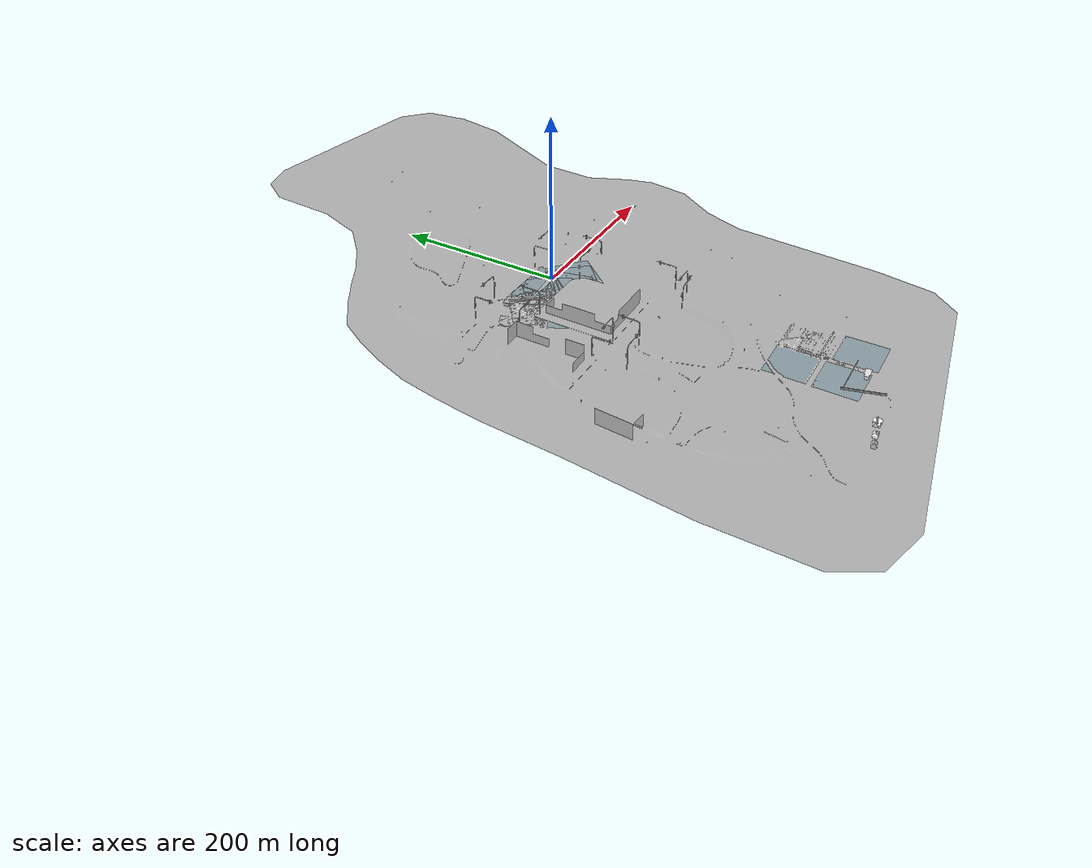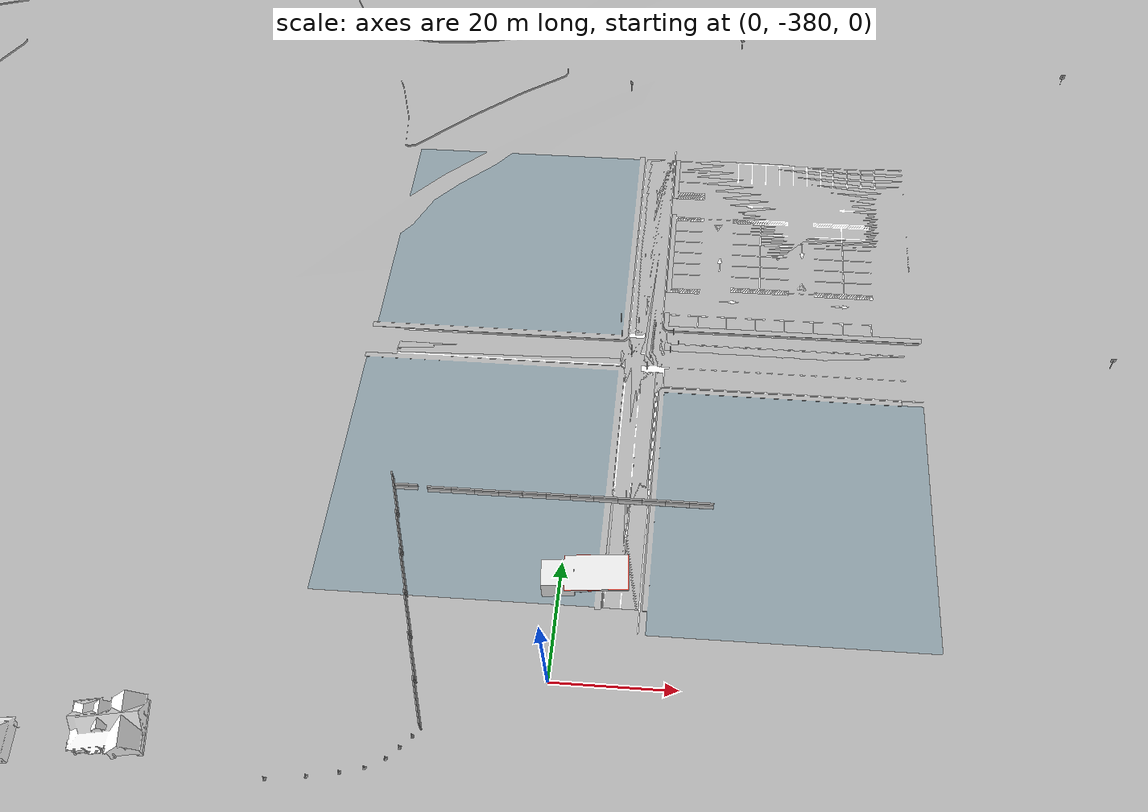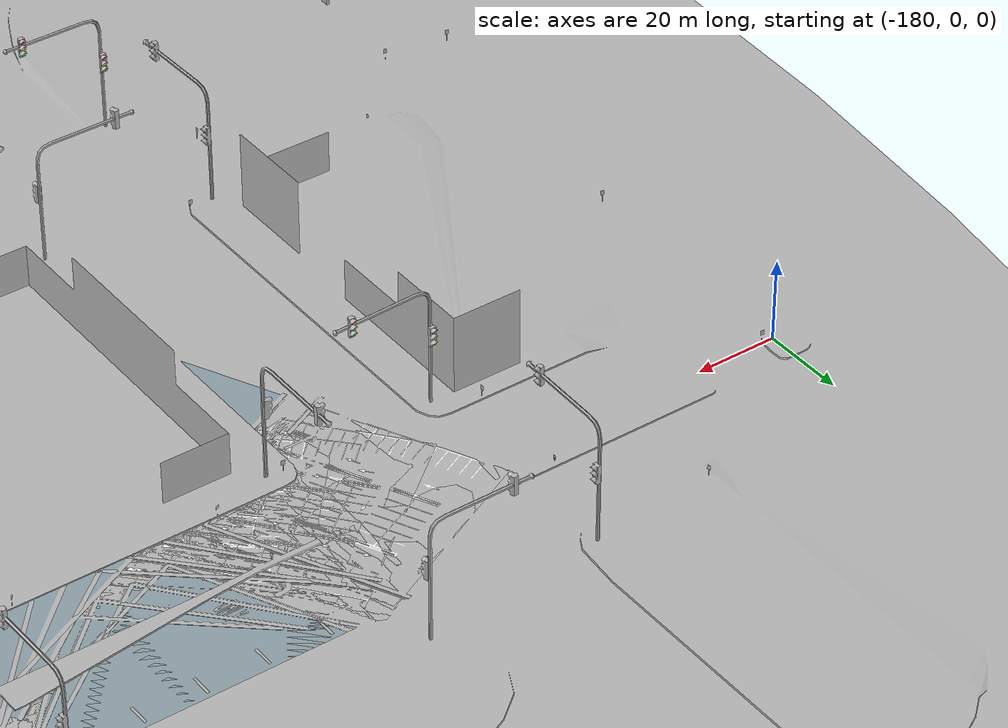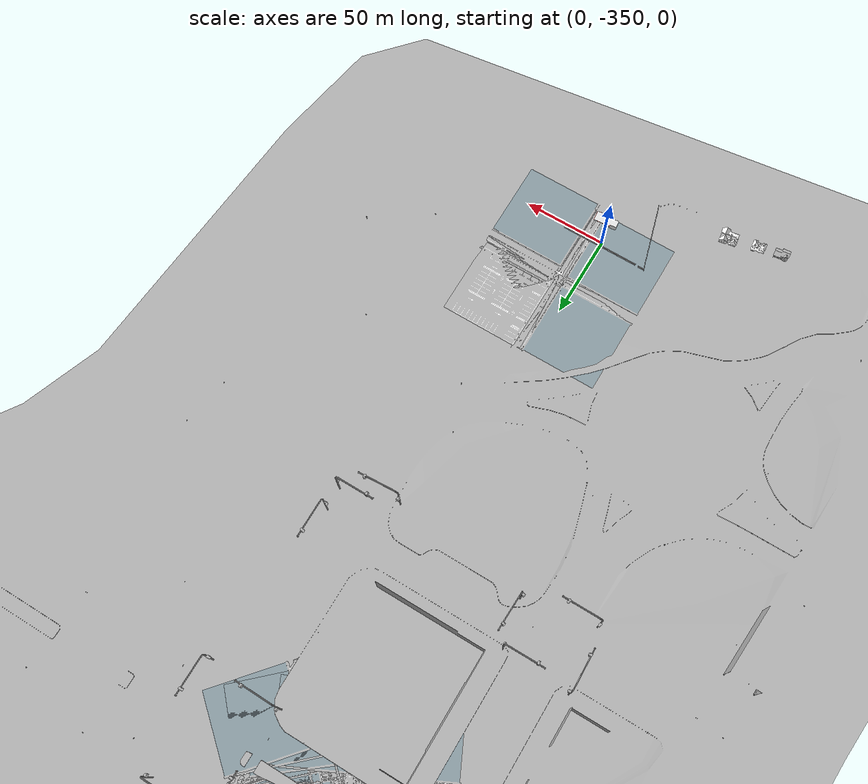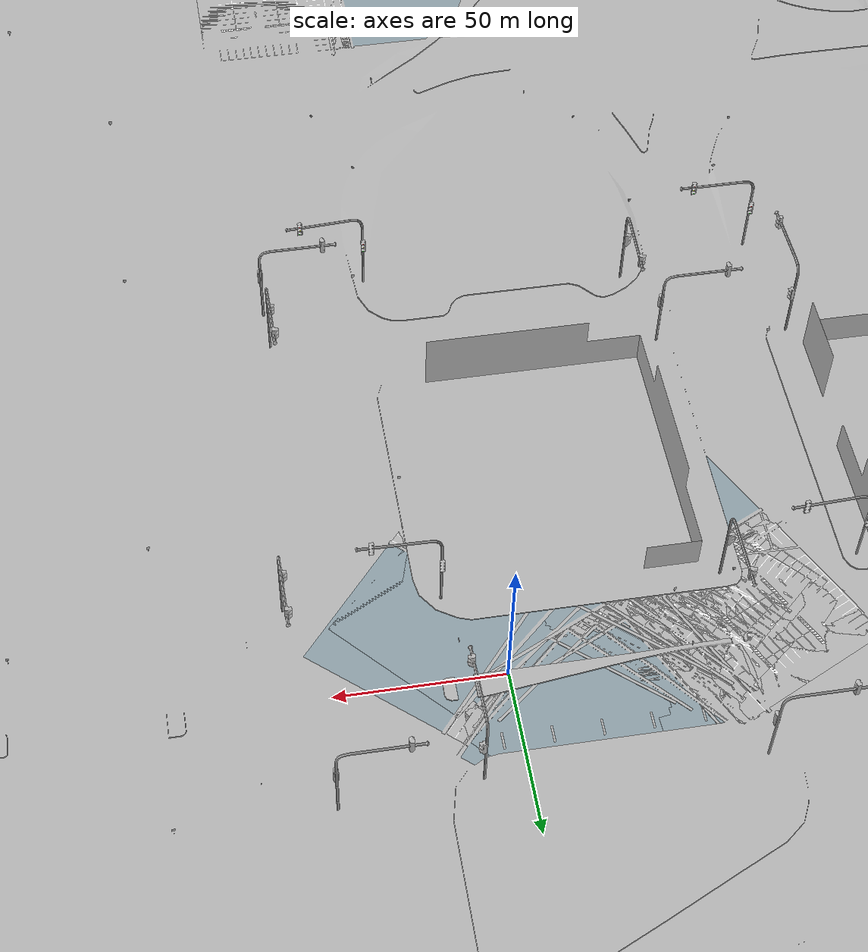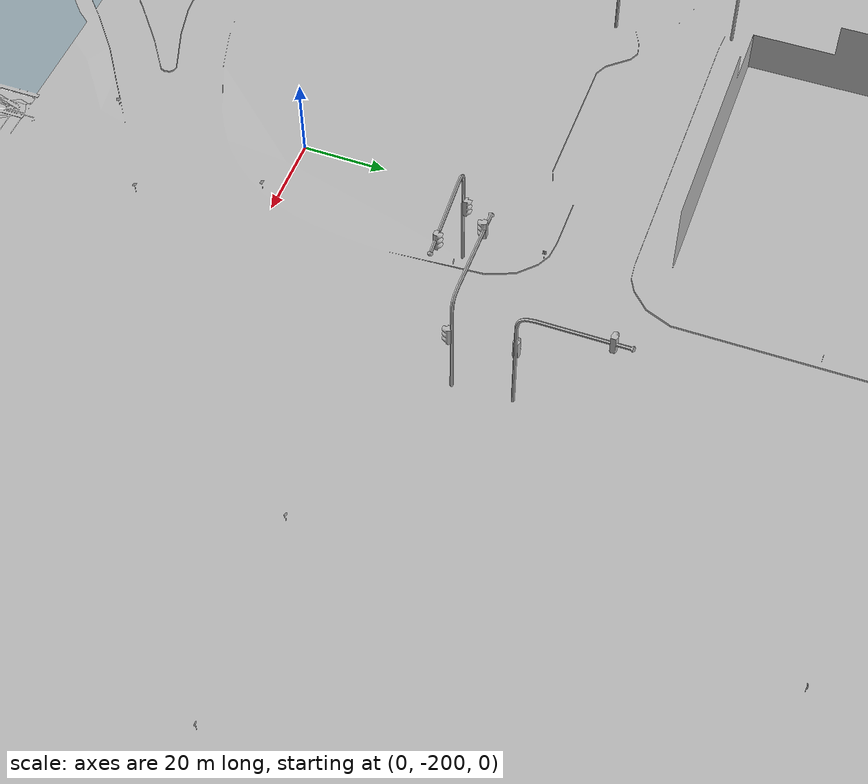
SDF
<sdf version="1.6">
 <world name="default">
  <light name="sun" type="directional">
   <pose>0 0 10 0 -0 0</pose>
   <diffuse>0.8 0.8 0.8 1</diffuse>
   <specular>0.2 0.2 0.2 1</specular>
   <attenuation>
    <range>1000</range>
    <constant>0.9</constant>
    <linear>0.01</linear>
    <quadratic>0.001</quadratic>
   </attenuation>
   <direction>-0.5 0.1 -0.9</direction>
  </light>
  <model name="cafe">
   <pose>0.038313 -0.078421 0 0 -0 0</pose>
   <static>1</static>
   <link name="link">
    <collision name="collision">
     <geometry><mesh><scale>0.254 0.254 0.254</scale><uri>model://mcity/meshes/mcity.obj</uri></mesh></geometry>
    </collision>
    <visual name="visual">
     <geometry><mesh><scale>0.254 0.254 0.254</scale><uri>model://mcity/meshes/mcity.obj</uri></mesh></geometry>
    </visual>
   </link>
  </model>
  <gravity>0 0 -9.8</gravity>
  <magnetic_field>6e-06 2.3e-05 -4.2e-05</magnetic_field>
  <atmosphere type="adiabatic"/>
  <physics name="default_physics" default="0" type="ode">
   <max_step_size>0.001</max_step_size>
   <real_time_factor>1</real_time_factor>
   <real_time_update_rate>1000</real_time_update_rate>
  </physics>
  <scene><ambient>0.4 0.4 0.4 1</ambient><background>0.7 0.7 0.7 1</background><shadows>1</shadows></scene>
  <audio><device>default</device></audio>
  <spherical_coordinates>
   <surface_model>EARTH_WGS84</surface_model>
   <latitude_deg>0</latitude_deg>
   <longitude_deg>0</longitude_deg>
   <elevation>0</elevation>
   <heading_deg>0</heading_deg>
  </spherical_coordinates>
  <model name="Gas Station">
   <static>1</static>
   <link name="link">
    <collision name="collision">
     <geometry><mesh><uri>model://gas_station/meshes/gas_station.dae</uri></mesh></geometry>
    </collision>
    <visual name="visual">
     <geometry><mesh><uri>model://gas_station/meshes/gas_station.dae</uri></mesh></geometry>
     <material>
      <script>
       <uri>model://gas_station/materials/scripts</uri>
       <uri>model://gas_station/materials/textures</uri>
       <name>GasStation/Diffuse</name>
      </script>
      <shader type="normal_map_object_space"><normal_map>GasStation_Normal.png</normal_map></shader>
     </material>
    </visual>
   </link>
   <pose>3.60098 -363.272 0 0 -0 0.083826</pose>
  </model>
  <model name="jersey_barrier">
   <static>1</static>
   <link name="link">
    <visual name="visual">
     <geometry><mesh><uri>model://jersey_barrier/meshes/jersey_barrier.dae</uri></mesh></geometry>
    </visual>
    <collision name="upright">
     <pose>0 0 0.5715 0 -0 0</pose>
     <geometry><box><size>4.06542 0.3063 1.143</size></box></geometry>
    </collision>
    <collision name="base">
     <pose>0 0 0.032258 0 -0 0</pose>
     <geometry><box><size>4.06542 0.8107 0.064516</size></box></geometry>
    </collision>
    <collision name="base2">
     <pose>0 0 0.1 0 -0 0</pose>
     <geometry><box><size>4.06542 0.65 0.1</size></box></geometry>
    </collision>
    <collision name="base3">
     <pose>0 0 0.2 0 -0 0</pose>
     <geometry><box><size>4.06542 0.5 0.1</size></box></geometry>
    </collision>
    <collision name="left-angle">
     <pose>0 -0.224 0.2401 0.9 -0 0</pose>
     <geometry><box><size>4.06542 0.5 0.064516</size></box></geometry>
    </collision>
    <collision name="right-angle">
     <pose>0 0.224 0.2401 -0.9 0 0</pose>
     <geometry><box><size>4.06542 0.5 0.064516</size></box></geometry>
    </collision>
   </link>
   <pose>-27.7486 -347.795 0 0 -0 0</pose>
  </model>
  <model name="jersey_barrier_clone">
   <static>1</static>
   <link name="link">
    <visual name="visual">
     <geometry><mesh><uri>model://jersey_barrier/meshes/jersey_barrier.dae</uri></mesh></geometry>
    </visual>
    <collision name="upright">
     <pose>0 0 0.5715 0 -0 0</pose>
     <geometry><box><size>4.06542 0.3063 1.143</size></box></geometry>
    </collision>
    <collision name="base">
     <pose>0 0 0.032258 0 -0 0</pose>
     <geometry><box><size>4.06542 0.8107 0.064516</size></box></geometry>
    </collision>
    <collision name="base2">
     <pose>0 0 0.1 0 -0 0</pose>
     <geometry><box><size>4.06542 0.65 0.1</size></box></geometry>
    </collision>
    <collision name="base3">
     <pose>0 0 0.2 0 -0 0</pose>
     <geometry><box><size>4.06542 0.5 0.1</size></box></geometry>
    </collision>
    <collision name="left-angle">
     <pose>0 -0.224 0.2401 0.9 -0 0</pose>
     <geometry><box><size>4.06542 0.5 0.064516</size></box></geometry>
    </collision>
    <collision name="right-angle">
     <pose>0 0.224 0.2401 -0.9 0 0</pose>
     <geometry><box><size>4.06542 0.5 0.064516</size></box></geometry>
    </collision>
   </link>
   <pose>-22 -348 0 0 -0 0</pose>
  </model>
  <model name="jersey_barrier_clone_clone">
   <static>1</static>
   <link name="link">
    <visual name="visual">
     <geometry><mesh><uri>model://jersey_barrier/meshes/jersey_barrier.dae</uri></mesh></geometry>
    </visual>
    <collision name="upright">
     <pose>0 0 0.5715 0 -0 0</pose>
     <geometry><box><size>4.06542 0.3063 1.143</size></box></geometry>
    </collision>
    <collision name="base">
     <pose>0 0 0.032258 0 -0 0</pose>
     <geometry><box><size>4.06542 0.8107 0.064516</size></box></geometry>
    </collision>
    <collision name="base2">
     <pose>0 0 0.1 0 -0 0</pose>
     <geometry><box><size>4.06542 0.65 0.1</size></box></geometry>
    </collision>
    <collision name="base3">
     <pose>0 0 0.2 0 -0 0</pose>
     <geometry><box><size>4.06542 0.5 0.1</size></box></geometry>
    </collision>
    <collision name="left-angle">
     <pose>0 -0.224 0.2401 0.9 -0 0</pose>
     <geometry><box><size>4.06542 0.5 0.064516</size></box></geometry>
    </collision>
    <collision name="right-angle">
     <pose>0 0.224 0.2401 -0.9 0 0</pose>
     <geometry><box><size>4.06542 0.5 0.064516</size></box></geometry>
    </collision>
   </link>
   <pose>-18 -348 0 0 -0 0</pose>
  </model>
  <model name="jersey_barrier_clone_clone_clone">
   <static>1</static>
   <link name="link">
    <visual name="visual">
     <geometry><mesh><uri>model://jersey_barrier/meshes/jersey_barrier.dae</uri></mesh></geometry>
    </visual>
    <collision name="upright">
     <pose>0 0 0.5715 0 -0 0</pose>
     <geometry><box><size>4.06542 0.3063 1.143</size></box></geometry>
    </collision>
    <collision name="base">
     <pose>0 0 0.032258 0 -0 0</pose>
     <geometry><box><size>4.06542 0.8107 0.064516</size></box></geometry>
    </collision>
    <collision name="base2">
     <pose>0 0 0.1 0 -0 0</pose>
     <geometry><box><size>4.06542 0.65 0.1</size></box></geometry>
    </collision>
    <collision name="base3">
     <pose>0 0 0.2 0 -0 0</pose>
     <geometry><box><size>4.06542 0.5 0.1</size></box></geometry>
    </collision>
    <collision name="left-angle">
     <pose>0 -0.224 0.2401 0.9 -0 0</pose>
     <geometry><box><size>4.06542 0.5 0.064516</size></box></geometry>
    </collision>
    <collision name="right-angle">
     <pose>0 0.224 0.2401 -0.9 0 0</pose>
     <geometry><box><size>4.06542 0.5 0.064516</size></box></geometry>
    </collision>
   </link>
   <pose>-14.0215 -348.019 0 0 -0 0</pose>
  </model>
  <model name="jersey_barrier_clone_clone_clone_clone">
   <static>1</static>
   <link name="link">
    <visual name="visual">
     <geometry><mesh><uri>model://jersey_barrier/meshes/jersey_barrier.dae</uri></mesh></geometry>
    </visual>
    <collision name="upright">
     <pose>0 0 0.5715 0 -0 0</pose>
     <geometry><box><size>4.06542 0.3063 1.143</size></box></geometry>
    </collision>
    <collision name="base">
     <pose>0 0 0.032258 0 -0 0</pose>
     <geometry><box><size>4.06542 0.8107 0.064516</size></box></geometry>
    </collision>
    <collision name="base2">
     <pose>0 0 0.1 0 -0 0</pose>
     <geometry><box><size>4.06542 0.65 0.1</size></box></geometry>
    </collision>
    <collision name="base3">
     <pose>0 0 0.2 0 -0 0</pose>
     <geometry><box><size>4.06542 0.5 0.1</size></box></geometry>
    </collision>
    <collision name="left-angle">
     <pose>0 -0.224 0.2401 0.9 -0 0</pose>
     <geometry><box><size>4.06542 0.5 0.064516</size></box></geometry>
    </collision>
    <collision name="right-angle">
     <pose>0 0.224 0.2401 -0.9 0 0</pose>
     <geometry><box><size>4.06542 0.5 0.064516</size></box></geometry>
    </collision>
   </link>
   <pose>-10 -348 0 0 -0 0</pose>
  </model>
  <model name="jersey_barrier_clone_clone_clone_clone_clone">
   <static>1</static>
   <link name="link">
    <visual name="visual">
     <geometry><mesh><uri>model://jersey_barrier/meshes/jersey_barrier.dae</uri></mesh></geometry>
    </visual>
    <collision name="upright">
     <pose>0 0 0.5715 0 -0 0</pose>
     <geometry><box><size>4.06542 0.3063 1.143</size></box></geometry>
    </collision>
    <collision name="base">
     <pose>0 0 0.032258 0 -0 0</pose>
     <geometry><box><size>4.06542 0.8107 0.064516</size></box></geometry>
    </collision>
    <collision name="base2">
     <pose>0 0 0.1 0 -0 0</pose>
     <geometry><box><size>4.06542 0.65 0.1</size></box></geometry>
    </collision>
    <collision name="base3">
     <pose>0 0 0.2 0 -0 0</pose>
     <geometry><box><size>4.06542 0.5 0.1</size></box></geometry>
    </collision>
    <collision name="left-angle">
     <pose>0 -0.224 0.2401 0.9 -0 0</pose>
     <geometry><box><size>4.06542 0.5 0.064516</size></box></geometry>
    </collision>
    <collision name="right-angle">
     <pose>0 0.224 0.2401 -0.9 0 0</pose>
     <geometry><box><size>4.06542 0.5 0.064516</size></box></geometry>
    </collision>
   </link>
   <pose>-6 -348 0 0 -0 0</pose>
  </model>
  <model name="jersey_barrier_clone_clone_clone_clone_clone_clone">
   <static>1</static>
   <link name="link">
    <visual name="visual">
     <geometry><mesh><uri>model://jersey_barrier/meshes/jersey_barrier.dae</uri></mesh></geometry>
    </visual>
    <collision name="upright">
     <pose>0 0 0.5715 0 -0 0</pose>
     <geometry><box><size>4.06542 0.3063 1.143</size></box></geometry>
    </collision>
    <collision name="base">
     <pose>0 0 0.032258 0 -0 0</pose>
     <geometry><box><size>4.06542 0.8107 0.064516</size></box></geometry>
    </collision>
    <collision name="base2">
     <pose>0 0 0.1 0 -0 0</pose>
     <geometry><box><size>4.06542 0.65 0.1</size></box></geometry>
    </collision>
    <collision name="base3">
     <pose>0 0 0.2 0 -0 0</pose>
     <geometry><box><size>4.06542 0.5 0.1</size></box></geometry>
    </collision>
    <collision name="left-angle">
     <pose>0 -0.224 0.2401 0.9 -0 0</pose>
     <geometry><box><size>4.06542 0.5 0.064516</size></box></geometry>
    </collision>
    <collision name="right-angle">
     <pose>0 0.224 0.2401 -0.9 0 0</pose>
     <geometry><box><size>4.06542 0.5 0.064516</size></box></geometry>
    </collision>
   </link>
   <pose>-2 -348 0 0 -0 0</pose>
  </model>
  <model name="jersey_barrier_clone_clone_clone_clone_clone_clone_clone">
   <static>1</static>
   <link name="link">
    <visual name="visual">
     <geometry><mesh><uri>model://jersey_barrier/meshes/jersey_barrier.dae</uri></mesh></geometry>
    </visual>
    <collision name="upright">
     <pose>0 0 0.5715 0 -0 0</pose>
     <geometry><box><size>4.06542 0.3063 1.143</size></box></geometry>
    </collision>
    <collision name="base">
     <pose>0 0 0.032258 0 -0 0</pose>
     <geometry><box><size>4.06542 0.8107 0.064516</size></box></geometry>
    </collision>
    <collision name="base2">
     <pose>0 0 0.1 0 -0 0</pose>
     <geometry><box><size>4.06542 0.65 0.1</size></box></geometry>
    </collision>
    <collision name="base3">
     <pose>0 0 0.2 0 -0 0</pose>
     <geometry><box><size>4.06542 0.5 0.1</size></box></geometry>
    </collision>
    <collision name="left-angle">
     <pose>0 -0.224 0.2401 0.9 -0 0</pose>
     <geometry><box><size>4.06542 0.5 0.064516</size></box></geometry>
    </collision>
    <collision name="right-angle">
     <pose>0 0.224 0.2401 -0.9 0 0</pose>
     <geometry><box><size>4.06542 0.5 0.064516</size></box></geometry>
    </collision>
   </link>
   <pose>6 -348 0 0 -0 0</pose>
  </model>
  <model name="jersey_barrier_clone_clone_clone_clone_clone_clone_clone_clone">
   <static>1</static>
   <link name="link">
    <visual name="visual">
     <geometry><mesh><uri>model://jersey_barrier/meshes/jersey_barrier.dae</uri></mesh></geometry>
    </visual>
    <collision name="upright">
     <pose>0 0 0.5715 0 -0 0</pose>
     <geometry><box><size>4.06542 0.3063 1.143</size></box></geometry>
    </collision>
    <collision name="base">
     <pose>0 0 0.032258 0 -0 0</pose>
     <geometry><box><size>4.06542 0.8107 0.064516</size></box></geometry>
    </collision>
    <collision name="base2">
     <pose>0 0 0.1 0 -0 0</pose>
     <geometry><box><size>4.06542 0.65 0.1</size></box></geometry>
    </collision>
    <collision name="base3">
     <pose>0 0 0.2 0 -0 0</pose>
     <geometry><box><size>4.06542 0.5 0.1</size></box></geometry>
    </collision>
    <collision name="left-angle">
     <pose>0 -0.224 0.2401 0.9 -0 0</pose>
     <geometry><box><size>4.06542 0.5 0.064516</size></box></geometry>
    </collision>
    <collision name="right-angle">
     <pose>0 0.224 0.2401 -0.9 0 0</pose>
     <geometry><box><size>4.06542 0.5 0.064516</size></box></geometry>
    </collision>
   </link>
   <pose>2 -348 0 0 -0 0</pose>
  </model>
  <model name="jersey_barrier_clone_clone_clone_clone_clone_clone_clone_clone_0">
   <static>1</static>
   <link name="link">
    <visual name="visual">
     <geometry><mesh><uri>model://jersey_barrier/meshes/jersey_barrier.dae</uri></mesh></geometry>
    </visual>
    <collision name="upright">
     <pose>0 0 0.5715 0 -0 0</pose>
     <geometry><box><size>4.06542 0.3063 1.143</size></box></geometry>
    </collision>
    <collision name="base">
     <pose>0 0 0.032258 0 -0 0</pose>
     <geometry><box><size>4.06542 0.8107 0.064516</size></box></geometry>
    </collision>
    <collision name="base2">
     <pose>0 0 0.1 0 -0 0</pose>
     <geometry><box><size>4.06542 0.65 0.1</size></box></geometry>
    </collision>
    <collision name="base3">
     <pose>0 0 0.2 0 -0 0</pose>
     <geometry><box><size>4.06542 0.5 0.1</size></box></geometry>
    </collision>
    <collision name="left-angle">
     <pose>0 -0.224 0.2401 0.9 -0 0</pose>
     <geometry><box><size>4.06542 0.5 0.064516</size></box></geometry>
    </collision>
    <collision name="right-angle">
     <pose>0 0.224 0.2401 -0.9 0 0</pose>
     <geometry><box><size>4.06542 0.5 0.064516</size></box></geometry>
    </collision>
   </link>
   <pose>10 -348 0 0 -0 0</pose>
  </model>
  <model name="jersey_barrier_clone_clone_clone_clone_clone_clone_clone_clone_0_clone">
   <static>1</static>
   <link name="link">
    <visual name="visual">
     <geometry><mesh><uri>model://jersey_barrier/meshes/jersey_barrier.dae</uri></mesh></geometry>
    </visual>
    <collision name="upright">
     <pose>0 0 0.5715 0 -0 0</pose>
     <geometry><box><size>4.06542 0.3063 1.143</size></box></geometry>
    </collision>
    <collision name="base">
     <pose>0 0 0.032258 0 -0 0</pose>
     <geometry><box><size>4.06542 0.8107 0.064516</size></box></geometry>
    </collision>
    <collision name="base2">
     <pose>0 0 0.1 0 -0 0</pose>
     <geometry><box><size>4.06542 0.65 0.1</size></box></geometry>
    </collision>
    <collision name="base3">
     <pose>0 0 0.2 0 -0 0</pose>
     <geometry><box><size>4.06542 0.5 0.1</size></box></geometry>
    </collision>
    <collision name="left-angle">
     <pose>0 -0.224 0.2401 0.9 -0 0</pose>
     <geometry><box><size>4.06542 0.5 0.064516</size></box></geometry>
    </collision>
    <collision name="right-angle">
     <pose>0 0.224 0.2401 -0.9 0 0</pose>
     <geometry><box><size>4.06542 0.5 0.064516</size></box></geometry>
    </collision>
   </link>
   <pose>14 -348 0 0 -0 0</pose>
  </model>
  <model name="jersey_barrier_clone_clone_clone_clone_clone_clone_clone_clone_0_clone_clone">
   <static>1</static>
   <link name="link">
    <visual name="visual">
     <geometry><mesh><uri>model://jersey_barrier/meshes/jersey_barrier.dae</uri></mesh></geometry>
    </visual>
    <collision name="upright">
     <pose>0 0 0.5715 0 -0 0</pose>
     <geometry><box><size>4.06542 0.3063 1.143</size></box></geometry>
    </collision>
    <collision name="base">
     <pose>0 0 0.032258 0 -0 0</pose>
     <geometry><box><size>4.06542 0.8107 0.064516</size></box></geometry>
    </collision>
    <collision name="base2">
     <pose>0 0 0.1 0 -0 0</pose>
     <geometry><box><size>4.06542 0.65 0.1</size></box></geometry>
    </collision>
    <collision name="base3">
     <pose>0 0 0.2 0 -0 0</pose>
     <geometry><box><size>4.06542 0.5 0.1</size></box></geometry>
    </collision>
    <collision name="left-angle">
     <pose>0 -0.224 0.2401 0.9 -0 0</pose>
     <geometry><box><size>4.06542 0.5 0.064516</size></box></geometry>
    </collision>
    <collision name="right-angle">
     <pose>0 0.224 0.2401 -0.9 0 0</pose>
     <geometry><box><size>4.06542 0.5 0.064516</size></box></geometry>
    </collision>
   </link>
   <pose>18 -348 0 0 -0 0</pose>
  </model>
  <model name="jersey_barrier_clone_clone_clone_clone_clone_clone_clone_clone_0_clone_clone_clone">
   <static>1</static>
   <link name="link">
    <visual name="visual">
     <geometry><mesh><uri>model://jersey_barrier/meshes/jersey_barrier.dae</uri></mesh></geometry>
    </visual>
    <collision name="upright">
     <pose>0 0 0.5715 0 -0 0</pose>
     <geometry><box><size>4.06542 0.3063 1.143</size></box></geometry>
    </collision>
    <collision name="base">
     <pose>0 0 0.032258 0 -0 0</pose>
     <geometry><box><size>4.06542 0.8107 0.064516</size></box></geometry>
    </collision>
    <collision name="base2">
     <pose>0 0 0.1 0 -0 0</pose>
     <geometry><box><size>4.06542 0.65 0.1</size></box></geometry>
    </collision>
    <collision name="base3">
     <pose>0 0 0.2 0 -0 0</pose>
     <geometry><box><size>4.06542 0.5 0.1</size></box></geometry>
    </collision>
    <collision name="left-angle">
     <pose>0 -0.224 0.2401 0.9 -0 0</pose>
     <geometry><box><size>4.06542 0.5 0.064516</size></box></geometry>
    </collision>
    <collision name="right-angle">
     <pose>0 0.224 0.2401 -0.9 0 0</pose>
     <geometry><box><size>4.06542 0.5 0.064516</size></box></geometry>
    </collision>
   </link>
   <pose>22 -348 0 0 -0 0</pose>
  </model>
  <model name="grey_wall">
   <static>1</static>
   <link name="link">
    <pose>0 0 1.4 0 -0 0</pose>
    <collision name="collision"><geometry><box><size>7.5 0.2 2.8</size></box></geometry></collision>
    <visual name="visual">
     <cast_shadows>0</cast_shadows>
     <geometry><box><size>7.5 0.2 2.8</size></box></geometry>
     <material>
      <script>
       <uri>model://grey_wall/materials/scripts</uri>
       <uri>model://grey_wall/materials/textures</uri>
       <name>vrc/grey_wall</name>
      </script>
     </material>
    </visual>
   </link>
   <pose>-29 -350 0 0 -0 1.87601</pose>
  </model>
  <model name="grey_wall_clone">
   <static>1</static>
   <link name="link">
    <pose>0 0 1.4 0 -0 0</pose>
    <collision name="collision"><geometry><box><size>7.5 0.2 2.8</size></box></geometry></collision>
    <visual name="visual">
     <cast_shadows>0</cast_shadows>
     <geometry><box><size>7.5 0.2 2.8</size></box></geometry>
     <material>
      <script>
       <uri>model://grey_wall/materials/scripts</uri>
       <uri>model://grey_wall/materials/textures</uri>
       <name>vrc/grey_wall</name>
      </script>
     </material>
    </visual>
   </link>
   <pose>-27 -357 0 0 -0 1.87601</pose>
  </model>
  <model name="grey_wall_clone_0">
   <static>1</static>
   <link name="link">
    <pose>0 0 1.4 0 -0 0</pose>
    <collision name="collision"><geometry><box><size>7.5 0.2 2.8</size></box></geometry></collision>
    <visual name="visual">
     <cast_shadows>0</cast_shadows>
     <geometry><box><size>7.5 0.2 2.8</size></box></geometry>
     <material>
      <script>
       <uri>model://grey_wall/materials/scripts</uri>
       <uri>model://grey_wall/materials/textures</uri>
       <name>vrc/grey_wall</name>
      </script>
     </material>
    </visual>
   </link>
   <pose>-25 -364 0 0 -0 1.87601</pose>
  </model>
  <model name="grey_wall_clone_0_clone">
   <static>1</static>
   <link name="link">
    <pose>0 0 1.4 0 -0 0</pose>
    <collision name="collision"><geometry><box><size>7.5 0.2 2.8</size></box></geometry></collision>
    <visual name="visual">
     <cast_shadows>0</cast_shadows>
     <geometry><box><size>7.5 0.2 2.8</size></box></geometry>
     <material>
      <script>
       <uri>model://grey_wall/materials/scripts</uri>
       <uri>model://grey_wall/materials/textures</uri>
       <name>vrc/grey_wall</name>
      </script>
     </material>
    </visual>
   </link>
   <pose>-23 -371 0 0 -0 1.87601</pose>
  </model>
  <model name="grey_wall_clone_0_clone_clone">
   <static>1</static>
   <link name="link">
    <pose>0 0 1.4 0 -0 0</pose>
    <collision name="collision"><geometry><box><size>7.5 0.2 2.8</size></box></geometry></collision>
    <visual name="visual">
     <cast_shadows>0</cast_shadows>
     <geometry><box><size>7.5 0.2 2.8</size></box></geometry>
     <material>
      <script>
       <uri>model://grey_wall/materials/scripts</uri>
       <uri>model://grey_wall/materials/textures</uri>
       <name>vrc/grey_wall</name>
      </script>
     </material>
    </visual>
   </link>
   <pose>-21 -378 0 0 -0 1.87601</pose>
  </model>
  <model name="grey_wall_clone_0_clone_clone_clone">
   <static>1</static>
   <link name="link">
    <pose>0 0 1.4 0 -0 0</pose>
    <collision name="collision"><geometry><box><size>7.5 0.2 2.8</size></box></geometry></collision>
    <visual name="visual">
     <cast_shadows>0</cast_shadows>
     <geometry><box><size>7.5 0.2 2.8</size></box></geometry>
     <material>
      <script>
       <uri>model://grey_wall/materials/scripts</uri>
       <uri>model://grey_wall/materials/textures</uri>
       <name>vrc/grey_wall</name>
      </script>
     </material>
    </visual>
   </link>
   <pose>-19 -385 0 0 -0 1.87601</pose>
  </model>
  <model name="House 1">
   <static>1</static>
   <link name="link">
    <collision name="collision">
     <geometry><mesh><uri>model://house_1/meshes/house_1.dae</uri></mesh></geometry>
    </collision>
    <visual name="visual">
     <geometry><mesh><uri>model://house_1/meshes/house_1.dae</uri></mesh></geometry>
     <material>
      <script>
       <uri>model://house_1/materials/scripts</uri>
       <uri>model://house_1/materials/textures</uri>
       <name>House_1/Diffuse</name>
      </script>
      <shader type="normal_map_object_space"><normal_map>House_1_Normal.png</normal_map></shader>
     </material>
    </visual>
   </link>
   <pose>-63.4144 -391.538 0 0 -0 0.178783</pose>
  </model>
  <model name="House 2">
   <static>1</static>
   <link name="link">
    <collision name="collision">
     <geometry><mesh><uri>model://house_2/meshes/house_2.dae</uri></mesh></geometry>
    </collision>
    <visual name="visual">
     <geometry><mesh><uri>model://house_2/meshes/house_2.dae</uri></mesh></geometry>
     <material>
      <script>
       <uri>model://house_2/materials/scripts</uri>
       <uri>model://house_2/materials/textures</uri>
       <uri>model://house_1/materials/textures</uri>
       <name>House_2/Diffuse</name>
      </script>
      <shader type="normal_map_object_space">
       <normal_map>model://house_1/materials/textures/House_1_Normal.png</normal_map>
      </shader>
     </material>
    </visual>
   </link>
   <pose>-82.0852 -395.523 0 0 -0 0.112755</pose>
  </model>
  <model name="House 3">
   <static>1</static>
   <link name="link">
    <collision name="collision">
     <geometry><mesh><uri>model://house_3/meshes/house_3.dae</uri></mesh></geometry>
    </collision>
    <visual name="visual">
     <geometry><mesh><uri>model://house_3/meshes/house_3.dae</uri></mesh></geometry>
     <material>
      <script>
       <uri>model://house_3/materials/scripts</uri>
       <uri>model://house_3/materials/textures</uri>
       <uri>model://house_1/materials/textures</uri>
       <name>House_3/Diffuse</name>
      </script>
      <shader type="normal_map_object_space">
       <normal_map>model://house_1/materials/textures/House_1_Normal.png</normal_map>
      </shader>
     </material>
    </visual>
   </link>
   <pose>-94.9389 -397.723 0 0 -0 0.112475</pose>
  </model>
  <model name="Construction Cone">
   <link name="link">
    <collision name="collision">
     <geometry>
      <mesh><scale>10 10 10</scale><uri>model://construction_cone/meshes/construction_cone.dae</uri></mesh>
     </geometry>
    </collision>
    <visual name="visual">
     <geometry>
      <mesh><scale>10 10 10</scale><uri>model://construction_cone/meshes/construction_cone.dae</uri></mesh>
     </geometry>
    </visual>
    <inertial>
     <inertia><ixx>1</ixx><ixy>0</ixy><ixz>0</ixz><iyy>1</iyy><iyz>0</iyz><izz>1</izz></inertia>
     <mass>1</mass>
    </inertial>
   </link>
   <pose>-19 -389.557 -9e-06 2e-06 -1e-06 -0</pose>
  </model>
  <model name="Construction Cone_clone">
   <link name="link">
    <collision name="collision">
     <geometry>
      <mesh><scale>10 10 10</scale><uri>model://construction_cone/meshes/construction_cone.dae</uri></mesh>
     </geometry>
    </collision>
    <visual name="visual">
     <geometry>
      <mesh><scale>10 10 10</scale><uri>model://construction_cone/meshes/construction_cone.dae</uri></mesh>
     </geometry>
    </visual>
    <inertial>
     <inertia><ixx>1</ixx><ixy>0</ixy><ixz>0</ixz><iyy>1</iyy><iyz>0</iyz><izz>1</izz></inertia>
     <mass>1</mass>
    </inertial>
   </link>
   <pose>-20.5705 -391.331 -0 -1e-06 -1e-06 0</pose>
  </model>
  <model name="Construction Cone_clone_clone">
   <link name="link">
    <collision name="collision">
     <geometry>
      <mesh><scale>10 10 10</scale><uri>model://construction_cone/meshes/construction_cone.dae</uri></mesh>
     </geometry>
    </collision>
    <visual name="visual">
     <geometry>
      <mesh><scale>10 10 10</scale><uri>model://construction_cone/meshes/construction_cone.dae</uri></mesh>
     </geometry>
    </visual>
    <inertial>
     <inertia><ixx>1</ixx><ixy>0</ixy><ixz>0</ixz><iyy>1</iyy><iyz>0</iyz><izz>1</izz></inertia>
     <mass>1</mass>
    </inertial>
   </link>
   <pose>-22.3249 -393.096 -9e-06 0 2e-06 0</pose>
  </model>
  <model name="Construction Cone_clone_clone_clone">
   <link name="link">
    <collision name="collision">
     <geometry>
      <mesh><scale>10 10 10</scale><uri>model://construction_cone/meshes/construction_cone.dae</uri></mesh>
     </geometry>
    </collision>
    <visual name="visual">
     <geometry>
      <mesh><scale>10 10 10</scale><uri>model://construction_cone/meshes/construction_cone.dae</uri></mesh>
     </geometry>
    </visual>
    <inertial>
     <inertia><ixx>1</ixx><ixy>0</ixy><ixz>0</ixz><iyy>1</iyy><iyz>0</iyz><izz>1</izz></inertia>
     <mass>1</mass>
    </inertial>
   </link>
   <pose>-25.1263 -394.655 -0 1e-06 -0 0</pose>
  </model>
  <model name="Construction Cone_clone_clone_clone_clone">
   <link name="link">
    <collision name="collision">
     <geometry>
      <mesh><scale>10 10 10</scale><uri>model://construction_cone/meshes/construction_cone.dae</uri></mesh>
     </geometry>
    </collision>
    <visual name="visual">
     <geometry>
      <mesh><scale>10 10 10</scale><uri>model://construction_cone/meshes/construction_cone.dae</uri></mesh>
     </geometry>
    </visual>
    <inertial>
     <inertia><ixx>1</ixx><ixy>0</ixy><ixz>0</ixz><iyy>1</iyy><iyz>0</iyz><izz>1</izz></inertia>
     <mass>1</mass>
    </inertial>
   </link>
   <pose>-28.6583 -395.535 0 0 -0 0</pose>
  </model>
  <model name="Construction Cone_clone_clone_clone_clone_clone">
   <link name="link">
    <collision name="collision">
     <geometry>
      <mesh><scale>10 10 10</scale><uri>model://construction_cone/meshes/construction_cone.dae</uri></mesh>
     </geometry>
    </collision>
    <visual name="visual">
     <geometry>
      <mesh><scale>10 10 10</scale><uri>model://construction_cone/meshes/construction_cone.dae</uri></mesh>
     </geometry>
    </visual>
    <inertial>
     <inertia><ixx>1</ixx><ixy>0</ixy><ixz>0</ixz><iyy>1</iyy><iyz>0</iyz><izz>1</izz></inertia>
     <mass>1</mass>
    </inertial>
   </link>
   <pose>-33.3133 -396.401 -0 0 -0 0</pose>
  </model>
  <model name="Construction Cone_clone_clone_clone_clone_clone_clone">
   <link name="link">
    <collision name="collision">
     <geometry>
      <mesh><scale>10 10 10</scale><uri>model://construction_cone/meshes/construction_cone.dae</uri></mesh>
     </geometry>
    </collision>
    <visual name="visual">
     <geometry>
      <mesh><scale>10 10 10</scale><uri>model://construction_cone/meshes/construction_cone.dae</uri></mesh>
     </geometry>
    </visual>
    <inertial>
     <inertia><ixx>1</ixx><ixy>0</ixy><ixz>0</ixz><iyy>1</iyy><iyz>0</iyz><izz>1</izz></inertia>
     <mass>1</mass>
    </inertial>
   </link>
   <pose>-39.2634 -397.191 -0 0 -0 0</pose>
  </model>
  <model name="cloverleaf_interchange">
   <static>1</static>
   <link name="link">
    <collision name="collision">
     <geometry>
      <mesh>
       <uri>model://cloverleaf_interchange/meshes/cloverleaf.obj</uri>
       <scale>0.0254 0.0254 0.0254</scale>
      </mesh>
     </geometry>
    </collision>
    <visual name="visual">
     <geometry>
      <mesh>
       <uri>model://cloverleaf_interchange/meshes/cloverleaf.obj</uri>
       <scale>0.0254 0.0254 0.0254</scale>
      </mesh>
     </geometry>
    </visual>
   </link>
   <pose>-295.324 348.572 0 0 -0 0</pose>
  </model>
  <model name="speed_10">
   <static>1</static>
   <link name="link">
    <collision name="collision">
     <geometry><mesh><scale>1 1 1</scale><uri>model://speed_10/meshes/speedlim_10.dae</uri></mesh></geometry>
    </collision>
    <visual name="visual">
     <geometry><mesh><scale>1 1 1</scale><uri>model://speed_10/meshes/speedlim_10.dae</uri></mesh></geometry>
    </visual>
   </link>
   <pose>16.3651 -314.509 0 0 -0 0</pose>
  </model>
  <model name="speed_15">
   <static>1</static>
   <link name="link">
    <collision name="collision">
     <geometry><mesh><scale>1 1 1</scale><uri>model://speed_15/meshes/speedlim_15.dae</uri></mesh></geometry>
    </collision>
    <visual name="visual">
     <geometry><mesh><scale>1 1 1</scale><uri>model://speed_15/meshes/speedlim_15.dae</uri></mesh></geometry>
    </visual>
   </link>
   <pose>15 -316.574 0 0 -0 0</pose>
  </model>
  <model name="speed_20">
   <static>1</static>
   <link name="link">
    <collision name="collision">
     <geometry><mesh><scale>1 1 1</scale><uri>model://speed_20/meshes/speedlim_20.dae</uri></mesh></geometry>
    </collision>
    <visual name="visual">
     <geometry><mesh><scale>1 1 1</scale><uri>model://speed_20/meshes/speedlim_20.dae</uri></mesh></geometry>
    </visual>
   </link>
   <pose>9 -318.347 0 0 -0 0</pose>
  </model>
  <model name="speed_25">
   <static>1</static>
   <link name="link">
    <collision name="collision">
     <geometry><mesh><scale>1 1 1</scale><uri>model://speed_25/meshes/speedlim_25.dae</uri></mesh></geometry>
    </collision>
    <visual name="visual">
     <geometry><mesh><scale>1 1 1</scale><uri>model://speed_25/meshes/speedlim_25.dae</uri></mesh></geometry>
    </visual>
   </link>
   <pose>8 -317.523 0 0 -0 0</pose>
  </model>
  <model name="stop">
   <static>1</static>
   <link name="link">
    <collision name="collision">
     <geometry><mesh><scale>1 1 1</scale><uri>model://stop/meshes/stop.dae</uri></mesh></geometry>
    </collision>
    <visual name="visual">
     <geometry><mesh><scale>1 1 1</scale><uri>model://stop/meshes/stop.dae</uri></mesh></geometry>
    </visual>
   </link>
   <pose>15.3575 -312.919 0 0 -0 0</pose>
  </model>
  <model name="yield">
   <static>1</static>
   <link name="link">
    <collision name="collision">
     <geometry><mesh><scale>1 1 1</scale><uri>model://yield/meshes/yield.dae</uri></mesh></geometry>
    </collision>
    <visual name="visual">
     <geometry><mesh><scale>1 1 1</scale><uri>model://yield/meshes/yield.dae</uri></mesh></geometry>
    </visual>
   </link>
   <pose>11.8551 -314.525 0 0 -0 0</pose>
  </model>
  <model name="pedestrain_walk">
   <static>1</static>
   <link name="link">
    <collision name="collision">
     <geometry>
      <mesh><scale>1 1 1</scale><uri>model://pedestrain_walk/meshes/pedestrain_walk.dae</uri></mesh>
     </geometry>
    </collision>
    <visual name="visual">
     <geometry>
      <mesh><scale>1 1 1</scale><uri>model://pedestrain_walk/meshes/pedestrain_walk.dae</uri></mesh>
     </geometry>
    </visual>
   </link>
   <pose>6 -313.945 0 0 -0 0</pose>
  </model>
  <model name="parking">
   <static>1</static>
   <link name="link">
    <collision name="collision">
     <geometry><mesh><scale>1 1 1</scale><uri>model://parking/meshes/parking.dae</uri></mesh></geometry>
    </collision>
    <visual name="visual">
     <geometry><mesh><scale>1 1 1</scale><uri>model://parking/meshes/parking.dae</uri></mesh></geometry>
    </visual>
   </link>
   <pose>10 -317.244 0 0 -0 0</pose>
  </model>
  <model name="no_parking">
   <static>1</static>
   <link name="link">
    <collision name="collision">
     <geometry><mesh><scale>1 1 1</scale><uri>model://no_parking/meshes/no_parking.dae</uri></mesh></geometry>
    </collision>
    <visual name="visual">
     <geometry><mesh><scale>1 1 1</scale><uri>model://no_parking/meshes/no_parking.dae</uri></mesh></geometry>
    </visual>
   </link>
   <pose>11 -320.613 0 0 -0 0</pose>
  </model>
  <model name="right_turn_only">
   <static>1</static>
   <link name="link">
    <collision name="collision">
     <geometry>
      <mesh><scale>1 1 1</scale><uri>model://right_turn_only/meshes/right_turn_only.dae</uri></mesh>
     </geometry>
    </collision>
    <visual name="visual">
     <geometry>
      <mesh><scale>1 1 1</scale><uri>model://right_turn_only/meshes/right_turn_only.dae</uri></mesh>
     </geometry>
    </visual>
   </link>
   <pose>8.85113 -311.338 0 0 -0 0</pose>
  </model>
  <model name="left_turn_only">
   <static>1</static>
   <link name="link">
    <collision name="collision">
     <geometry>
      <mesh><scale>1 1 1</scale><uri>model://left_turn_only/meshes/left_turn_only.dae</uri></mesh>
     </geometry>
    </collision>
    <visual name="visual">
     <geometry>
      <mesh><scale>1 1 1</scale><uri>model://left_turn_only/meshes/left_turn_only.dae</uri></mesh>
     </geometry>
    </visual>
   </link>
   <pose>9.95826 -313.03 0 0 -0 0</pose>
  </model>
  <model name="gas_station_sign">
   <static>1</static>
   <link name="link">
    <collision name="collision">
     <geometry>
      <mesh><scale>1 1 1</scale><uri>model://gas_station_sign/meshes/gas_station_sign.dae</uri></mesh>
     </geometry>
    </collision>
    <visual name="visual">
     <geometry>
      <mesh><scale>1 1 1</scale><uri>model://gas_station_sign/meshes/gas_station_sign.dae</uri></mesh>
     </geometry>
    </visual>
   </link>
   <pose>12.0199 -312.397 0 0 -0 0</pose>
  </model>
  <model name="do_not_enter">
   <static>1</static>
   <link name="link">
    <collision name="collision">
     <geometry><mesh><scale>1 1 1</scale><uri>model://do_not_enter/meshes/do_not_enter.dae</uri></mesh></geometry>
    </collision>
    <visual name="visual">
     <geometry><mesh><scale>1 1 1</scale><uri>model://do_not_enter/meshes/do_not_enter.dae</uri></mesh></geometry>
    </visual>
   </link>
   <pose>5.52846 -310.301 0 0 -0 0</pose>
  </model>
  <model name="disabled_parking">
   <static>1</static>
   <link name="link">
    <collision name="collision">
     <geometry>
      <mesh><scale>1 1 1</scale><uri>model://disabled_parking/meshes/disabled_parking.dae</uri></mesh>
     </geometry>
    </collision>
    <visual name="visual">
     <geometry>
      <mesh><scale>1 1 1</scale><uri>model://disabled_parking/meshes/disabled_parking.dae</uri></mesh>
     </geometry>
    </visual>
   </link>
   <pose>11.4731 -319.106 0 0 -0 0</pose>
  </model>
  <model name="speed_20_clone">
   <static>1</static>
   <link name="link">
    <collision name="collision">
     <geometry><mesh><scale>1 1 1</scale><uri>model://speed_20/meshes/speedlim_20.dae</uri></mesh></geometry>
    </collision>
    <visual name="visual">
     <geometry><mesh><scale>1 1 1</scale><uri>model://speed_20/meshes/speedlim_20.dae</uri></mesh></geometry>
    </visual>
   </link>
   <pose>138.704 -25.0728 -0.003717 0.003542 -0.07679 -1.61694</pose>
  </model>
  <model name="do_not_enter_clone">
   <static>1</static>
   <link name="link">
    <collision name="collision">
     <geometry><mesh><scale>1 1 1</scale><uri>model://do_not_enter/meshes/do_not_enter.dae</uri></mesh></geometry>
    </collision>
    <visual name="visual">
     <geometry><mesh><scale>1 1 1</scale><uri>model://do_not_enter/meshes/do_not_enter.dae</uri></mesh></geometry>
    </visual>
   </link>
   <pose>2.61951 -247.104 0 0 -0 0.58137</pose>
  </model>
  <model name="right_turn_only_clone">
   <static>1</static>
   <link name="link">
    <collision name="collision">
     <geometry>
      <mesh><scale>1 1 1</scale><uri>model://right_turn_only/meshes/right_turn_only.dae</uri></mesh>
     </geometry>
    </collision>
    <visual name="visual">
     <geometry>
      <mesh><scale>1 1 1</scale><uri>model://right_turn_only/meshes/right_turn_only.dae</uri></mesh>
     </geometry>
    </visual>
   </link>
   <pose>-49.3964 -232.327 0 0 -0 0</pose>
  </model>
  <model name="pedestrain_walk_clone">
   <static>1</static>
   <link name="link">
    <collision name="collision">
     <geometry>
      <mesh><scale>1 1 1</scale><uri>model://pedestrain_walk/meshes/pedestrain_walk.dae</uri></mesh>
     </geometry>
    </collision>
    <visual name="visual">
     <geometry>
      <mesh><scale>1 1 1</scale><uri>model://pedestrain_walk/meshes/pedestrain_walk.dae</uri></mesh>
     </geometry>
    </visual>
   </link>
   <pose>-63.9132 -217.257 0 0 0 -1.27558</pose>
  </model>
  <model name="pedestrain_walk_clone_0">
   <static>1</static>
   <link name="link">
    <collision name="collision">
     <geometry>
      <mesh><scale>1 1 1</scale><uri>model://pedestrain_walk/meshes/pedestrain_walk.dae</uri></mesh>
     </geometry>
    </collision>
    <visual name="visual">
     <geometry>
      <mesh><scale>1 1 1</scale><uri>model://pedestrain_walk/meshes/pedestrain_walk.dae</uri></mesh>
     </geometry>
    </visual>
   </link>
   <pose>-106.211 -186.474 0 0 -0 1.33811</pose>
  </model>
  <model name="pedestrain_walk_clone_1">
   <static>1</static>
   <link name="link">
    <collision name="collision">
     <geometry>
      <mesh><scale>1 1 1</scale><uri>model://pedestrain_walk/meshes/pedestrain_walk.dae</uri></mesh>
     </geometry>
    </collision>
    <visual name="visual">
     <geometry>
      <mesh><scale>1 1 1</scale><uri>model://pedestrain_walk/meshes/pedestrain_walk.dae</uri></mesh>
     </geometry>
    </visual>
   </link>
   <pose>26.1097 -231.394 0 0 0 -2.21802</pose>
  </model>
  <model name="pedestrain_walk_clone_2">
   <static>1</static>
   <link name="link">
    <collision name="collision">
     <geometry>
      <mesh><scale>1 1 1</scale><uri>model://pedestrain_walk/meshes/pedestrain_walk.dae</uri></mesh>
     </geometry>
    </collision>
    <visual name="visual">
     <geometry>
      <mesh><scale>1 1 1</scale><uri>model://pedestrain_walk/meshes/pedestrain_walk.dae</uri></mesh>
     </geometry>
    </visual>
   </link>
   <pose>15.2697 -204.239 0 0 -0 0.947326</pose>
  </model>
  <model name="right_turn_only_clone_1">
   <static>1</static>
   <link name="link">
    <collision name="collision">
     <geometry>
      <mesh><scale>1 1 1</scale><uri>model://right_turn_only/meshes/right_turn_only.dae</uri></mesh>
     </geometry>
    </collision>
    <visual name="visual">
     <geometry>
      <mesh><scale>1 1 1</scale><uri>model://right_turn_only/meshes/right_turn_only.dae</uri></mesh>
     </geometry>
    </visual>
   </link>
   <pose>13.1429 -136.452 0 0 -0 3.07373</pose>
  </model>
  <model name="left_turn_only_clone">
   <static>1</static>
   <link name="link">
    <collision name="collision">
     <geometry>
      <mesh><scale>1 1 1</scale><uri>model://left_turn_only/meshes/left_turn_only.dae</uri></mesh>
     </geometry>
    </collision>
    <visual name="visual">
     <geometry>
      <mesh><scale>1 1 1</scale><uri>model://left_turn_only/meshes/left_turn_only.dae</uri></mesh>
     </geometry>
    </visual>
   </link>
   <pose>-105.194 -111.726 0 0 -0 1.56016</pose>
  </model>
  <model name="right_turn_only_clone_2">
   <static>1</static>
   <link name="link">
    <collision name="collision">
     <geometry>
      <mesh><scale>1 1 1</scale><uri>model://right_turn_only/meshes/right_turn_only.dae</uri></mesh>
     </geometry>
    </collision>
    <visual name="visual">
     <geometry>
      <mesh><scale>1 1 1</scale><uri>model://right_turn_only/meshes/right_turn_only.dae</uri></mesh>
     </geometry>
    </visual>
   </link>
   <pose>-118.173 -19.9532 0 0 -0 3.13054</pose>
  </model>
  <model name="right_turn_only_clone_3">
   <static>1</static>
   <link name="link">
    <collision name="collision">
     <geometry>
      <mesh><scale>1 1 1</scale><uri>model://right_turn_only/meshes/right_turn_only.dae</uri></mesh>
     </geometry>
    </collision>
    <visual name="visual">
     <geometry>
      <mesh><scale>1 1 1</scale><uri>model://right_turn_only/meshes/right_turn_only.dae</uri></mesh>
     </geometry>
    </visual>
   </link>
   <pose>-71.0591 -23.7095 0 0 0 -1.70966</pose>
  </model>
  <model name="left_turn_only_clone_0">
   <static>1</static>
   <link name="link">
    <collision name="collision">
     <geometry>
      <mesh><scale>1 1 1</scale><uri>model://left_turn_only/meshes/left_turn_only.dae</uri></mesh>
     </geometry>
    </collision>
    <visual name="visual">
     <geometry>
      <mesh><scale>1 1 1</scale><uri>model://left_turn_only/meshes/left_turn_only.dae</uri></mesh>
     </geometry>
    </visual>
   </link>
   <pose>-177.298 -0.58583 0 0 -0 1.51381</pose>
  </model>
  <model name="right_turn_only_clone_4">
   <static>1</static>
   <link name="link">
    <collision name="collision">
     <geometry>
      <mesh><scale>1 1 1</scale><uri>model://right_turn_only/meshes/right_turn_only.dae</uri></mesh>
     </geometry>
    </collision>
    <visual name="visual">
     <geometry>
      <mesh><scale>1 1 1</scale><uri>model://right_turn_only/meshes/right_turn_only.dae</uri></mesh>
     </geometry>
    </visual>
   </link>
   <pose>28.8738 216.307 0 0 -0 1.57736</pose>
  </model>
  <model name="left_turn_only_clone_1">
   <static>1</static>
   <link name="link">
    <collision name="collision">
     <geometry>
      <mesh><scale>1 1 1</scale><uri>model://left_turn_only/meshes/left_turn_only.dae</uri></mesh>
     </geometry>
    </collision>
    <visual name="visual">
     <geometry>
      <mesh><scale>1 1 1</scale><uri>model://left_turn_only/meshes/left_turn_only.dae</uri></mesh>
     </geometry>
    </visual>
   </link>
   <pose>-116.673 7.19164 0 0 -0 3.05826</pose>
  </model>
  <model name="disabled_parking_clone">
   <static>1</static>
   <link name="link">
    <collision name="collision">
     <geometry>
      <mesh><scale>1 1 1</scale><uri>model://disabled_parking/meshes/disabled_parking.dae</uri></mesh>
     </geometry>
    </collision>
    <visual name="visual">
     <geometry>
      <mesh><scale>1 1 1</scale><uri>model://disabled_parking/meshes/disabled_parking.dae</uri></mesh>
     </geometry>
    </visual>
   </link>
   <pose>-52.5378 -19.6503 0 0 -0 1.97264</pose>
  </model>
  <model name="parking_clone">
   <static>1</static>
   <link name="link">
    <collision name="collision">
     <geometry><mesh><scale>1 1 1</scale><uri>model://parking/meshes/parking.dae</uri></mesh></geometry>
    </collision>
    <visual name="visual">
     <geometry><mesh><scale>1 1 1</scale><uri>model://parking/meshes/parking.dae</uri></mesh></geometry>
    </visual>
   </link>
   <pose>-41.8213 -19.7691 0 0 -0 2.02162</pose>
  </model>
  <model name="parking_clone_0">
   <static>1</static>
   <link name="link">
    <collision name="collision">
     <geometry><mesh><scale>1 1 1</scale><uri>model://parking/meshes/parking.dae</uri></mesh></geometry>
    </collision>
    <visual name="visual">
     <geometry><mesh><scale>1 1 1</scale><uri>model://parking/meshes/parking.dae</uri></mesh></geometry>
    </visual>
   </link>
   <pose>-31.3363 -19.9482 0 0 -0 2.24615</pose>
  </model>
  <model name="parking_clone_1">
   <static>1</static>
   <link name="link">
    <collision name="collision">
     <geometry><mesh><scale>1 1 1</scale><uri>model://parking/meshes/parking.dae</uri></mesh></geometry>
    </collision>
    <visual name="visual">
     <geometry><mesh><scale>1 1 1</scale><uri>model://parking/meshes/parking.dae</uri></mesh></geometry>
    </visual>
   </link>
   <pose>-22.5647 -20.1733 0 0 -0 2.31822</pose>
  </model>
  <model name="parking_clone_2">
   <static>1</static>
   <link name="link">
    <collision name="collision">
     <geometry><mesh><scale>1 1 1</scale><uri>model://parking/meshes/parking.dae</uri></mesh></geometry>
    </collision>
    <visual name="visual">
     <geometry><mesh><scale>1 1 1</scale><uri>model://parking/meshes/parking.dae</uri></mesh></geometry>
    </visual>
   </link>
   <pose>-14.3255 -19.943 0 0 -0 2.43218</pose>
  </model>
  <model name="disabled_parking_clone_0">
   <static>1</static>
   <link name="link">
    <collision name="collision">
     <geometry>
      <mesh><scale>1 1 1</scale><uri>model://disabled_parking/meshes/disabled_parking.dae</uri></mesh>
     </geometry>
    </collision>
    <visual name="visual">
     <geometry>
      <mesh><scale>1 1 1</scale><uri>model://disabled_parking/meshes/disabled_parking.dae</uri></mesh>
     </geometry>
    </visual>
   </link>
   <pose>-5.23545 -20.1233 0 0 -0 2.29508</pose>
  </model>
  <model name="left_turn_only_clone_2">
   <static>1</static>
   <link name="link">
    <collision name="collision">
     <geometry>
      <mesh><scale>1 1 1</scale><uri>model://left_turn_only/meshes/left_turn_only.dae</uri></mesh>
     </geometry>
    </collision>
    <visual name="visual">
     <geometry>
      <mesh><scale>1 1 1</scale><uri>model://left_turn_only/meshes/left_turn_only.dae</uri></mesh>
     </geometry>
    </visual>
   </link>
   <pose>-53.3552 -1.06942 0 0 -0 0</pose>
  </model>
  <model name="left_turn_only_clone_3">
   <static>1</static>
   <link name="link">
    <collision name="collision">
     <geometry>
      <mesh><scale>1 1 1</scale><uri>model://left_turn_only/meshes/left_turn_only.dae</uri></mesh>
     </geometry>
    </collision>
    <visual name="visual">
     <geometry>
      <mesh><scale>1 1 1</scale><uri>model://left_turn_only/meshes/left_turn_only.dae</uri></mesh>
     </geometry>
    </visual>
   </link>
   <pose>71.6014 -19.9846 0 0 -0 0</pose>
  </model>
  <model name="speed_10_clone">
   <static>1</static>
   <link name="link">
    <collision name="collision">
     <geometry><mesh><scale>1 1 1</scale><uri>model://speed_10/meshes/speedlim_10.dae</uri></mesh></geometry>
    </collision>
    <visual name="visual">
     <geometry><mesh><scale>1 1 1</scale><uri>model://speed_10/meshes/speedlim_10.dae</uri></mesh></geometry>
    </visual>
   </link>
   <pose>22.2362 -154.73 0 0 -0 1.58279</pose>
  </model>
  <model name="speed_15_clone_0">
   <static>1</static>
   <link name="link">
    <collision name="collision">
     <geometry><mesh><scale>1 1 1</scale><uri>model://speed_15/meshes/speedlim_15.dae</uri></mesh></geometry>
    </collision>
    <visual name="visual">
     <geometry><mesh><scale>1 1 1</scale><uri>model://speed_15/meshes/speedlim_15.dae</uri></mesh></geometry>
    </visual>
   </link>
   <pose>19.9355 -71.5133 0 0 -0 1.52793</pose>
  </model>
  <model name="right_turn_only_clone_clone">
   <static>1</static>
   <link name="link">
    <collision name="collision">
     <geometry>
      <mesh><scale>1 1 1</scale><uri>model://right_turn_only/meshes/right_turn_only.dae</uri></mesh>
     </geometry>
    </collision>
    <visual name="visual">
     <geometry>
      <mesh><scale>1 1 1</scale><uri>model://right_turn_only/meshes/right_turn_only.dae</uri></mesh>
     </geometry>
    </visual>
   </link>
   <pose>72.4478 23.7977 0 0 -0 0</pose>
  </model>
  <model name="speed_25_clone">
   <static>1</static>
   <link name="link">
    <collision name="collision">
     <geometry><mesh><scale>1 1 1</scale><uri>model://speed_25/meshes/speedlim_25.dae</uri></mesh></geometry>
    </collision>
    <visual name="visual">
     <geometry><mesh><scale>1 1 1</scale><uri>model://speed_25/meshes/speedlim_25.dae</uri></mesh></geometry>
    </visual>
   </link>
   <pose>128.12 -291.74 0 0 0 -1.64596</pose>
  </model>
  <model name="speed_20_clone">
   <static>1</static>
   <link name="link">
    <collision name="collision">
     <geometry><mesh><scale>1 1 1</scale><uri>model://speed_20/meshes/speedlim_20.dae</uri></mesh></geometry>
    </collision>
    <visual name="visual">
     <geometry><mesh><scale>1 1 1</scale><uri>model://speed_20/meshes/speedlim_20.dae</uri></mesh></geometry>
    </visual>
   </link>
   <pose>138.704 -25.0728 -0.003717 0.003542 -0.07679 -1.61694</pose>
  </model>
  <model name="speed_20_clone_0">
   <static>1</static>
   <link name="link">
    <collision name="collision">
     <geometry><mesh><scale>1 1 1</scale><uri>model://speed_20/meshes/speedlim_20.dae</uri></mesh></geometry>
    </collision>
    <visual name="visual">
     <geometry><mesh><scale>1 1 1</scale><uri>model://speed_20/meshes/speedlim_20.dae</uri></mesh></geometry>
    </visual>
   </link>
   <pose>137.621 96.4771 0 0 0 -1.63187</pose>
  </model>
  <model name="stop_clone">
   <static>1</static>
   <link name="link">
    <collision name="collision">
     <geometry><mesh><scale>1 1 1</scale><uri>model://stop/meshes/stop.dae</uri></mesh></geometry>
    </collision>
    <visual name="visual">
     <geometry><mesh><scale>1 1 1</scale><uri>model://stop/meshes/stop.dae</uri></mesh></geometry>
    </visual>
   </link>
   <pose>131.173 317.298 0 0 0 -1.57863</pose>
  </model>
  <model name="speed_25_clone_0">
   <static>1</static>
   <link name="link">
    <collision name="collision">
     <geometry><mesh><scale>1 1 1</scale><uri>model://speed_25/meshes/speedlim_25.dae</uri></mesh></geometry>
    </collision>
    <visual name="visual">
     <geometry><mesh><scale>1 1 1</scale><uri>model://speed_25/meshes/speedlim_25.dae</uri></mesh></geometry>
    </visual>
   </link>
   <pose>99.2627 309.814 0 0 -0 1.42965</pose>
  </model>
  <model name="speed_25_clone_1">
   <static>1</static>
   <link name="link">
    <collision name="collision">
     <geometry><mesh><scale>1 1 1</scale><uri>model://speed_25/meshes/speedlim_25.dae</uri></mesh></geometry>
    </collision>
    <visual name="visual">
     <geometry><mesh><scale>1 1 1</scale><uri>model://speed_25/meshes/speedlim_25.dae</uri></mesh></geometry>
    </visual>
   </link>
   <pose>97.9334 166.673 0 0 -0 1.69161</pose>
  </model>
  <model name="stop_clone_0">
   <static>1</static>
   <link name="link">
    <collision name="collision">
     <geometry><mesh><scale>1 1 1</scale><uri>model://stop/meshes/stop.dae</uri></mesh></geometry>
    </collision>
    <visual name="visual">
     <geometry><mesh><scale>1 1 1</scale><uri>model://stop/meshes/stop.dae</uri></mesh></geometry>
    </visual>
   </link>
   <pose>142.626 23.6306 0 0 -0 0</pose>
  </model>
  <model name="speed_25_clone_2">
   <static>1</static>
   <link name="link">
    <collision name="collision">
     <geometry><mesh><scale>1 1 1</scale><uri>model://speed_25/meshes/speedlim_25.dae</uri></mesh></geometry>
    </collision>
    <visual name="visual">
     <geometry><mesh><scale>1 1 1</scale><uri>model://speed_25/meshes/speedlim_25.dae</uri></mesh></geometry>
    </visual>
   </link>
   <pose>97.046 34.9881 0 0 -0 1.52611</pose>
  </model>
  <model name="speed_25_clone_3">
   <static>1</static>
   <link name="link">
    <collision name="collision">
     <geometry><mesh><scale>1 1 1</scale><uri>model://speed_25/meshes/speedlim_25.dae</uri></mesh></geometry>
    </collision>
    <visual name="visual">
     <geometry><mesh><scale>1 1 1</scale><uri>model://speed_25/meshes/speedlim_25.dae</uri></mesh></geometry>
    </visual>
   </link>
   <pose>96.5104 -57.1357 0 0 -0 1.92209</pose>
  </model>
  <model name="stop_clone_1">
   <static>1</static>
   <link name="link">
    <collision name="collision">
     <geometry><mesh><scale>1 1 1</scale><uri>model://stop/meshes/stop.dae</uri></mesh></geometry>
    </collision>
    <visual name="visual">
     <geometry><mesh><scale>1 1 1</scale><uri>model://stop/meshes/stop.dae</uri></mesh></geometry>
    </visual>
   </link>
   <pose>94.2599 -314.743 0 0 -0 1.60627</pose>
  </model>
  <model name="yield_clone">
   <static>1</static>
   <link name="link">
    <collision name="collision">
     <geometry><mesh><scale>1 1 1</scale><uri>model://yield/meshes/yield.dae</uri></mesh></geometry>
    </collision>
    <visual name="visual">
     <geometry><mesh><scale>1 1 1</scale><uri>model://yield/meshes/yield.dae</uri></mesh></geometry>
    </visual>
   </link>
   <pose>142.904 -161.978 0 0 0 -1.5877</pose>
  </model>
  <model name="yield_clone_0">
   <static>1</static>
   <link name="link">
    <collision name="collision">
     <geometry><mesh><scale>1 1 1</scale><uri>model://yield/meshes/yield.dae</uri></mesh></geometry>
    </collision>
    <visual name="visual">
     <geometry><mesh><scale>1 1 1</scale><uri>model://yield/meshes/yield.dae</uri></mesh></geometry>
    </visual>
   </link>
   <pose>142.182 94.617 0 0 -0 1.36275</pose>
  </model>
  <model name="stop_clone_4">
   <static>1</static>
   <link name="link">
    <collision name="collision">
     <geometry><mesh><scale>1 1 1</scale><uri>model://stop/meshes/stop.dae</uri></mesh></geometry>
    </collision>
    <visual name="visual">
     <geometry><mesh><scale>1 1 1</scale><uri>model://stop/meshes/stop.dae</uri></mesh></geometry>
    </visual>
   </link>
   <pose>217.695 -30.2795 0 0 0 -1.62504</pose>
  </model>
  <model name="right_turn_only_clone_0">
   <static>1</static>
   <link name="link">
    <collision name="collision">
     <geometry>
      <mesh><scale>1 1 1</scale><uri>model://right_turn_only/meshes/right_turn_only.dae</uri></mesh>
     </geometry>
    </collision>
    <visual name="visual">
     <geometry>
      <mesh><scale>1 1 1</scale><uri>model://right_turn_only/meshes/right_turn_only.dae</uri></mesh>
     </geometry>
    </visual>
   </link>
   <pose>-140.1 28.1404 0 0 -0 0</pose>
  </model>
  <model name="stop_clone_5">
   <static>1</static>
   <link name="link">
    <collision name="collision">
     <geometry><mesh><scale>1 1 1</scale><uri>model://stop/meshes/stop.dae</uri></mesh></geometry>
    </collision>
    <visual name="visual">
     <geometry><mesh><scale>1 1 1</scale><uri>model://stop/meshes/stop.dae</uri></mesh></geometry>
    </visual>
   </link>
   <pose>-156.088 -116.56 0 0 -0 0</pose>
  </model>
  <model name="speed_20_clone_2">
   <static>1</static>
   <link name="link">
    <collision name="collision">
     <geometry><mesh><scale>1 1 1</scale><uri>model://speed_20/meshes/speedlim_20.dae</uri></mesh></geometry>
    </collision>
    <visual name="visual">
     <geometry><mesh><scale>1 1 1</scale><uri>model://speed_20/meshes/speedlim_20.dae</uri></mesh></geometry>
    </visual>
   </link>
   <pose>-181.053 -61.1568 0 0 -0 1.31496</pose>
  </model>
  <model name="speed_20_clone_3">
   <static>1</static>
   <link name="link">
    <collision name="collision">
     <geometry><mesh><scale>1 1 1</scale><uri>model://speed_20/meshes/speedlim_20.dae</uri></mesh></geometry>
    </collision>
    <visual name="visual">
     <geometry><mesh><scale>1 1 1</scale><uri>model://speed_20/meshes/speedlim_20.dae</uri></mesh></geometry>
    </visual>
   </link>
   <pose>-174.614 -136.256 0 0 0 -1.70534</pose>
  </model>
  <model name="speed_15_clone_1">
   <static>1</static>
   <link name="link">
    <collision name="collision">
     <geometry><mesh><scale>1 1 1</scale><uri>model://speed_15/meshes/speedlim_15.dae</uri></mesh></geometry>
    </collision>
    <visual name="visual">
     <geometry><mesh><scale>1 1 1</scale><uri>model://speed_15/meshes/speedlim_15.dae</uri></mesh></geometry>
    </visual>
   </link>
   <pose>-191.035 -134.503 0 0 -0 1.36068</pose>
  </model>
  <model name="speed_15_clone_2">
   <static>1</static>
   <link name="link">
    <collision name="collision">
     <geometry><mesh><scale>1 1 1</scale><uri>model://speed_15/meshes/speedlim_15.dae</uri></mesh></geometry>
    </collision>
    <visual name="visual">
     <geometry><mesh><scale>1 1 1</scale><uri>model://speed_15/meshes/speedlim_15.dae</uri></mesh></geometry>
    </visual>
   </link>
   <pose>-183.024 -244.322 0 0 0 -1.64691</pose>
  </model>
  <model name="speed_20_clone_4">
   <static>1</static>
   <link name="link">
    <collision name="collision">
     <geometry><mesh><scale>1 1 1</scale><uri>model://speed_20/meshes/speedlim_20.dae</uri></mesh></geometry>
    </collision>
    <visual name="visual">
     <geometry><mesh><scale>1 1 1</scale><uri>model://speed_20/meshes/speedlim_20.dae</uri></mesh></geometry>
    </visual>
   </link>
   <pose>-197.569 -217.917 0 0 -0 1.58802</pose>
  </model>
  <model name="stop_clone_6">
   <static>1</static>
   <link name="link">
    <collision name="collision">
     <geometry><mesh><scale>1 1 1</scale><uri>model://stop/meshes/stop.dae</uri></mesh></geometry>
    </collision>
    <visual name="visual">
     <geometry><mesh><scale>1 1 1</scale><uri>model://stop/meshes/stop.dae</uri></mesh></geometry>
    </visual>
   </link>
   <pose>-164.034 -361.03 0 0 -0 0.414646</pose>
  </model>
  <model name="yield_clone_1">
   <static>1</static>
   <link name="link">
    <collision name="collision">
     <geometry><mesh><scale>1 1 1</scale><uri>model://yield/meshes/yield.dae</uri></mesh></geometry>
    </collision>
    <visual name="visual">
     <geometry><mesh><scale>1 1 1</scale><uri>model://yield/meshes/yield.dae</uri></mesh></geometry>
    </visual>
   </link>
   <pose>-117.342 -314.011 0 0 -0 0</pose>
  </model>
  <model name="yield_clone_2">
   <static>1</static>
   <link name="link">
    <collision name="collision">
     <geometry><mesh><scale>1 1 1</scale><uri>model://yield/meshes/yield.dae</uri></mesh></geometry>
    </collision>
    <visual name="visual">
     <geometry><mesh><scale>1 1 1</scale><uri>model://yield/meshes/yield.dae</uri></mesh></geometry>
    </visual>
   </link>
   <pose>-147.784 -273.478 0 0 -0 2.72153</pose>
  </model>
  <model name="yield_clone_3">
   <static>1</static>
   <link name="link">
    <collision name="collision">
     <geometry><mesh><scale>1 1 1</scale><uri>model://yield/meshes/yield.dae</uri></mesh></geometry>
    </collision>
    <visual name="visual">
     <geometry><mesh><scale>1 1 1</scale><uri>model://yield/meshes/yield.dae</uri></mesh></geometry>
    </visual>
   </link>
   <pose>-117.274 -208.655 0 0 -0 1.01276</pose>
  </model>
  <model name="stop_clone_7">
   <static>1</static>
   <link name="link">
    <collision name="collision">
     <geometry><mesh><scale>1 1 1</scale><uri>model://stop/meshes/stop.dae</uri></mesh></geometry>
    </collision>
    <visual name="visual">
     <geometry><mesh><scale>1 1 1</scale><uri>model://stop/meshes/stop.dae</uri></mesh></geometry>
    </visual>
   </link>
   <pose>147.806 -132.577 0 0 -0 0.637861</pose>
  </model>
  <model name="stop_clone_8">
   <static>1</static>
   <link name="link">
    <collision name="collision">
     <geometry><mesh><scale>1 1 1</scale><uri>model://stop/meshes/stop.dae</uri></mesh></geometry>
    </collision>
    <visual name="visual">
     <geometry><mesh><scale>1 1 1</scale><uri>model://stop/meshes/stop.dae</uri></mesh></geometry>
    </visual>
   </link>
   <pose>57.6121 153.536 0 0 -0 0.398427</pose>
  </model>
  <model name="stop_clone_9">
   <static>1</static>
   <link name="link">
    <collision name="collision">
     <geometry><mesh><scale>1 1 1</scale><uri>model://stop/meshes/stop.dae</uri></mesh></geometry>
    </collision>
    <visual name="visual">
     <geometry><mesh><scale>1 1 1</scale><uri>model://stop/meshes/stop.dae</uri></mesh></geometry>
    </visual>
   </link>
   <pose>55.6974 214.71 0 0 -0 0</pose>
  </model>
  <model name="speed_15_clone_3">
   <static>1</static>
   <link name="link">
    <collision name="collision">
     <geometry><mesh><scale>1 1 1</scale><uri>model://speed_15/meshes/speedlim_15.dae</uri></mesh></geometry>
    </collision>
    <visual name="visual">
     <geometry><mesh><scale>1 1 1</scale><uri>model://speed_15/meshes/speedlim_15.dae</uri></mesh></geometry>
    </visual>
   </link>
   <pose>-74.2401 -174.664 0 0 0 -1.53902</pose>
  </model>
  <model name="speed_25_clone_4">
   <static>1</static>
   <link name="link">
    <collision name="collision">
     <geometry><mesh><scale>1 1 1</scale><uri>model://speed_25/meshes/speedlim_25.dae</uri></mesh></geometry>
    </collision>
    <visual name="visual">
     <geometry><mesh><scale>1 1 1</scale><uri>model://speed_25/meshes/speedlim_25.dae</uri></mesh></geometry>
    </visual>
   </link>
   <pose>95.6403 -164.038 0 0 -0 1.35926</pose>
  </model>
  <model name="speed_20_clone_1">
   <static>1</static>
   <link name="link">
    <collision name="collision">
     <geometry><mesh><scale>1 1 1</scale><uri>model://speed_20/meshes/speedlim_20.dae</uri></mesh></geometry>
    </collision>
    <visual name="visual">
     <geometry><mesh><scale>1 1 1</scale><uri>model://speed_20/meshes/speedlim_20.dae</uri></mesh></geometry>
    </visual>
   </link>
   <pose>95.2595 -238.769 0 0 -0 1.42326</pose>
  </model>
  <model name="stop_clone_2">
   <static>1</static>
   <link name="link">
    <collision name="collision">
     <geometry><mesh><scale>1 1 1</scale><uri>model://stop/meshes/stop.dae</uri></mesh></geometry>
    </collision>
    <visual name="visual">
     <geometry><mesh><scale>1 1 1</scale><uri>model://stop/meshes/stop.dae</uri></mesh></geometry>
    </visual>
   </link>
   <pose>-121.558 -134.72 0 0 -0 3.09551</pose>
  </model>
  <model name="stop_light_post">
   <static>1</static>
   <link name="link">
    <collision name="post">
     <geometry>
      <mesh><uri>model://stop_light_post/meshes/stop_light_post.obj</uri><scale>0.05 0.05 0.05</scale></mesh>
     </geometry>
    </collision>
    <visual name="post">
     <geometry>
      <mesh><uri>model://stop_light_post/meshes/stop_light_post.obj</uri><scale>0.05 0.05 0.05</scale></mesh>
     </geometry>
    </visual>
   </link>
   <static>1</static>
   <link name="right_light::link">
    <collision name="collision">
     <geometry>
      <mesh><uri>model://stop_light/meshes/stop_light.obj</uri><scale>0.06 0.06 0.06</scale></mesh>
     </geometry>
    </collision>
    <visual name="frame">
     <geometry>
      <mesh><uri>model://stop_light/meshes/stop_light.obj</uri><scale>0.06 0.06 0.06</scale></mesh>
     </geometry>
    </visual>
    <visual name="red">
     <pose>-0.06738 -0.493506 -0.885084 0 -0 0</pose>
     <geometry><sphere><radius>0.66</radius></sphere></geometry>
     <material>
      <script>
       <uri>model://stop_light/materials/scripts/</uri>
       <uri>model://stop_light/materials/textures/</uri>
       <name>StopLight/Light</name>
      </script>
      <ambient>1 0 0 1</ambient>
      <specular>1 0 0 1</specular>
     </material>
    </visual>
    <visual name="yellow">
     <pose>-0.06738 -0.493506 -2.412 0 -0 0</pose>
     <geometry><sphere><radius>0.66</radius></sphere></geometry>
     <material>
      <script>
       <uri>model://stop_light/materials/scripts/</uri>
       <uri>model://stop_light/materials/textures/</uri>
       <name>StopLight/Light</name>
      </script>
      <ambient>1 1 0 1</ambient>
      <specular>1 1 0 1</specular>
     </material>
    </visual>
    <visual name="green">
     <pose>-0.06738 -0.493506 -3.93 0 -0 0</pose>
     <geometry><sphere><radius>0.66</radius></sphere></geometry>
     <material>
      <script>
       <uri>model://stop_light/materials/scripts/</uri>
       <uri>model://stop_light/materials/textures/</uri>
       <name>StopLight/Light</name>
      </script>
      <ambient>0 1 0 1</ambient>
      <specular>0 1 0 1</specular>
     </material>
    </visual>
    <pose>0 -0.25 20 0 -0 0</pose>
   </link>
   <static>1</static>
   <link name="center_light::link">
    <collision name="collision">
     <geometry>
      <mesh><uri>model://stop_light/meshes/stop_light.obj</uri><scale>0.06 0.06 0.06</scale></mesh>
     </geometry>
    </collision>
    <visual name="frame">
     <geometry>
      <mesh><uri>model://stop_light/meshes/stop_light.obj</uri><scale>0.06 0.06 0.06</scale></mesh>
     </geometry>
    </visual>
    <visual name="red">
     <pose>-0.06738 -0.493506 -0.885084 0 -0 0</pose>
     <geometry><sphere><radius>0.66</radius></sphere></geometry>
     <material>
      <script>
       <uri>model://stop_light/materials/scripts/</uri>
       <uri>model://stop_light/materials/textures/</uri>
       <name>StopLight/Light</name>
      </script>
      <ambient>1 0 0 1</ambient>
      <specular>1 0 0 1</specular>
     </material>
    </visual>
    <visual name="yellow">
     <pose>-0.06738 -0.493506 -2.412 0 -0 0</pose>
     <geometry><sphere><radius>0.66</radius></sphere></geometry>
     <material>
      <script>
       <uri>model://stop_light/materials/scripts/</uri>
       <uri>model://stop_light/materials/textures/</uri>
       <name>StopLight/Light</name>
      </script>
      <ambient>1 1 0 1</ambient>
      <specular>1 1 0 1</specular>
     </material>
    </visual>
    <visual name="green">
     <pose>-0.06738 -0.493506 -3.93 0 -0 0</pose>
     <geometry><sphere><radius>0.66</radius></sphere></geometry>
     <material>
      <script>
       <uri>model://stop_light/materials/scripts/</uri>
       <uri>model://stop_light/materials/textures/</uri>
       <name>StopLight/Light</name>
      </script>
      <ambient>0 1 0 1</ambient>
      <specular>0 1 0 1</specular>
     </material>
    </visual>
    <pose>-20 0.2 31.5 0 -0 0</pose>
   </link>
   <pose>52.9861 34.5132 0 0 -0 0</pose>
  </model>
  <model name="stop_light_post_0">
   <static>1</static>
   <link name="link">
    <collision name="post">
     <geometry>
      <mesh><uri>model://stop_light_post/meshes/stop_light_post.obj</uri><scale>0.05 0.05 0.05</scale></mesh>
     </geometry>
    </collision>
    <visual name="post">
     <geometry>
      <mesh><uri>model://stop_light_post/meshes/stop_light_post.obj</uri><scale>0.05 0.05 0.05</scale></mesh>
     </geometry>
    </visual>
   </link>
   <static>1</static>
   <link name="right_light::link">
    <collision name="collision">
     <geometry>
      <mesh><uri>model://stop_light/meshes/stop_light.obj</uri><scale>0.06 0.06 0.06</scale></mesh>
     </geometry>
    </collision>
    <visual name="frame">
     <geometry>
      <mesh><uri>model://stop_light/meshes/stop_light.obj</uri><scale>0.06 0.06 0.06</scale></mesh>
     </geometry>
    </visual>
    <visual name="red">
     <pose>-0.06738 -0.493506 -0.885084 0 -0 0</pose>
     <geometry><sphere><radius>0.66</radius></sphere></geometry>
     <material>
      <script>
       <uri>model://stop_light/materials/scripts/</uri>
       <uri>model://stop_light/materials/textures/</uri>
       <name>StopLight/Light</name>
      </script>
      <ambient>1 0 0 1</ambient>
      <specular>1 0 0 1</specular>
     </material>
    </visual>
    <visual name="yellow">
     <pose>-0.06738 -0.493506 -2.412 0 -0 0</pose>
     <geometry><sphere><radius>0.66</radius></sphere></geometry>
     <material>
      <script>
       <uri>model://stop_light/materials/scripts/</uri>
       <uri>model://stop_light/materials/textures/</uri>
       <name>StopLight/Light</name>
      </script>
      <ambient>1 1 0 1</ambient>
      <specular>1 1 0 1</specular>
     </material>
    </visual>
    <visual name="green">
     <pose>-0.06738 -0.493506 -3.93 0 -0 0</pose>
     <geometry><sphere><radius>0.66</radius></sphere></geometry>
     <material>
      <script>
       <uri>model://stop_light/materials/scripts/</uri>
       <uri>model://stop_light/materials/textures/</uri>
       <name>StopLight/Light</name>
      </script>
      <ambient>0 1 0 1</ambient>
      <specular>0 1 0 1</specular>
     </material>
    </visual>
    <pose>0 -0.25 20 0 -0 0</pose>
   </link>
   <static>1</static>
   <link name="center_light::link">
    <collision name="collision">
     <geometry>
      <mesh><uri>model://stop_light/meshes/stop_light.obj</uri><scale>0.06 0.06 0.06</scale></mesh>
     </geometry>
    </collision>
    <visual name="frame">
     <geometry>
      <mesh><uri>model://stop_light/meshes/stop_light.obj</uri><scale>0.06 0.06 0.06</scale></mesh>
     </geometry>
    </visual>
    <visual name="red">
     <pose>-0.06738 -0.493506 -0.885084 0 -0 0</pose>
     <geometry><sphere><radius>0.66</radius></sphere></geometry>
     <material>
      <script>
       <uri>model://stop_light/materials/scripts/</uri>
       <uri>model://stop_light/materials/textures/</uri>
       <name>StopLight/Light</name>
      </script>
      <ambient>1 0 0 1</ambient>
      <specular>1 0 0 1</specular>
     </material>
    </visual>
    <visual name="yellow">
     <pose>-0.06738 -0.493506 -2.412 0 -0 0</pose>
     <geometry><sphere><radius>0.66</radius></sphere></geometry>
     <material>
      <script>
       <uri>model://stop_light/materials/scripts/</uri>
       <uri>model://stop_light/materials/textures/</uri>
       <name>StopLight/Light</name>
      </script>
      <ambient>1 1 0 1</ambient>
      <specular>1 1 0 1</specular>
     </material>
    </visual>
    <visual name="green">
     <pose>-0.06738 -0.493506 -3.93 0 -0 0</pose>
     <geometry><sphere><radius>0.66</radius></sphere></geometry>
     <material>
      <script>
       <uri>model://stop_light/materials/scripts/</uri>
       <uri>model://stop_light/materials/textures/</uri>
       <name>StopLight/Light</name>
      </script>
      <ambient>0 1 0 1</ambient>
      <specular>0 1 0 1</specular>
     </material>
    </visual>
    <pose>-20 0.2 31.5 0 -0 0</pose>
   </link>
   <pose>12.5319 31.493 0 0 -0 1.58769</pose>
  </model>
  <model name="stop_light_post_2">
   <static>1</static>
   <link name="link">
    <collision name="post">
     <geometry>
      <mesh><uri>model://stop_light_post/meshes/stop_light_post.obj</uri><scale>0.05 0.05 0.05</scale></mesh>
     </geometry>
    </collision>
    <visual name="post">
     <geometry>
      <mesh><uri>model://stop_light_post/meshes/stop_light_post.obj</uri><scale>0.05 0.05 0.05</scale></mesh>
     </geometry>
    </visual>
   </link>
   <static>1</static>
   <link name="right_light::link">
    <collision name="collision">
     <geometry>
      <mesh><uri>model://stop_light/meshes/stop_light.obj</uri><scale>0.06 0.06 0.06</scale></mesh>
     </geometry>
    </collision>
    <visual name="frame">
     <geometry>
      <mesh><uri>model://stop_light/meshes/stop_light.obj</uri><scale>0.06 0.06 0.06</scale></mesh>
     </geometry>
    </visual>
    <visual name="red">
     <pose>-0.06738 -0.493506 -0.885084 0 -0 0</pose>
     <geometry><sphere><radius>0.66</radius></sphere></geometry>
     <material>
      <script>
       <uri>model://stop_light/materials/scripts/</uri>
       <uri>model://stop_light/materials/textures/</uri>
       <name>StopLight/Light</name>
      </script>
      <ambient>1 0 0 1</ambient>
      <specular>1 0 0 1</specular>
     </material>
    </visual>
    <visual name="yellow">
     <pose>-0.06738 -0.493506 -2.412 0 -0 0</pose>
     <geometry><sphere><radius>0.66</radius></sphere></geometry>
     <material>
      <script>
       <uri>model://stop_light/materials/scripts/</uri>
       <uri>model://stop_light/materials/textures/</uri>
       <name>StopLight/Light</name>
      </script>
      <ambient>1 1 0 1</ambient>
      <specular>1 1 0 1</specular>
     </material>
    </visual>
    <visual name="green">
     <pose>-0.06738 -0.493506 -3.93 0 -0 0</pose>
     <geometry><sphere><radius>0.66</radius></sphere></geometry>
     <material>
      <script>
       <uri>model://stop_light/materials/scripts/</uri>
       <uri>model://stop_light/materials/textures/</uri>
       <name>StopLight/Light</name>
      </script>
      <ambient>0 1 0 1</ambient>
      <specular>0 1 0 1</specular>
     </material>
    </visual>
    <pose>0 -0.25 20 0 -0 0</pose>
   </link>
   <static>1</static>
   <link name="center_light::link">
    <collision name="collision">
     <geometry>
      <mesh><uri>model://stop_light/meshes/stop_light.obj</uri><scale>0.06 0.06 0.06</scale></mesh>
     </geometry>
    </collision>
    <visual name="frame">
     <geometry>
      <mesh><uri>model://stop_light/meshes/stop_light.obj</uri><scale>0.06 0.06 0.06</scale></mesh>
     </geometry>
    </visual>
    <visual name="red">
     <pose>-0.06738 -0.493506 -0.885084 0 -0 0</pose>
     <geometry><sphere><radius>0.66</radius></sphere></geometry>
     <material>
      <script>
       <uri>model://stop_light/materials/scripts/</uri>
       <uri>model://stop_light/materials/textures/</uri>
       <name>StopLight/Light</name>
      </script>
      <ambient>1 0 0 1</ambient>
      <specular>1 0 0 1</specular>
     </material>
    </visual>
    <visual name="yellow">
     <pose>-0.06738 -0.493506 -2.412 0 -0 0</pose>
     <geometry><sphere><radius>0.66</radius></sphere></geometry>
     <material>
      <script>
       <uri>model://stop_light/materials/scripts/</uri>
       <uri>model://stop_light/materials/textures/</uri>
       <name>StopLight/Light</name>
      </script>
      <ambient>1 1 0 1</ambient>
      <specular>1 1 0 1</specular>
     </material>
    </visual>
    <visual name="green">
     <pose>-0.06738 -0.493506 -3.93 0 -0 0</pose>
     <geometry><sphere><radius>0.66</radius></sphere></geometry>
     <material>
      <script>
       <uri>model://stop_light/materials/scripts/</uri>
       <uri>model://stop_light/materials/textures/</uri>
       <name>StopLight/Light</name>
      </script>
      <ambient>0 1 0 1</ambient>
      <specular>0 1 0 1</specular>
     </material>
    </visual>
    <pose>-20 0.2 31.5 0 -0 0</pose>
   </link>
   <pose>14.4321 -28.0554 0 0 -0 3.12386</pose>
  </model>
  <model name="stop_light_post_1">
   <static>1</static>
   <link name="link">
    <collision name="post">
     <geometry>
      <mesh><uri>model://stop_light_post/meshes/stop_light_post.obj</uri><scale>0.05 0.05 0.05</scale></mesh>
     </geometry>
    </collision>
    <visual name="post">
     <geometry>
      <mesh><uri>model://stop_light_post/meshes/stop_light_post.obj</uri><scale>0.05 0.05 0.05</scale></mesh>
     </geometry>
    </visual>
   </link>
   <static>1</static>
   <link name="right_light::link">
    <collision name="collision">
     <geometry>
      <mesh><uri>model://stop_light/meshes/stop_light.obj</uri><scale>0.06 0.06 0.06</scale></mesh>
     </geometry>
    </collision>
    <visual name="frame">
     <geometry>
      <mesh><uri>model://stop_light/meshes/stop_light.obj</uri><scale>0.06 0.06 0.06</scale></mesh>
     </geometry>
    </visual>
    <visual name="red">
     <pose>-0.06738 -0.493506 -0.885084 0 -0 0</pose>
     <geometry><sphere><radius>0.66</radius></sphere></geometry>
     <material>
      <script>
       <uri>model://stop_light/materials/scripts/</uri>
       <uri>model://stop_light/materials/textures/</uri>
       <name>StopLight/Light</name>
      </script>
      <ambient>1 0 0 1</ambient>
      <specular>1 0 0 1</specular>
     </material>
    </visual>
    <visual name="yellow">
     <pose>-0.06738 -0.493506 -2.412 0 -0 0</pose>
     <geometry><sphere><radius>0.66</radius></sphere></geometry>
     <material>
      <script>
       <uri>model://stop_light/materials/scripts/</uri>
       <uri>model://stop_light/materials/textures/</uri>
       <name>StopLight/Light</name>
      </script>
      <ambient>1 1 0 1</ambient>
      <specular>1 1 0 1</specular>
     </material>
    </visual>
    <visual name="green">
     <pose>-0.06738 -0.493506 -3.93 0 -0 0</pose>
     <geometry><sphere><radius>0.66</radius></sphere></geometry>
     <material>
      <script>
       <uri>model://stop_light/materials/scripts/</uri>
       <uri>model://stop_light/materials/textures/</uri>
       <name>StopLight/Light</name>
      </script>
      <ambient>0 1 0 1</ambient>
      <specular>0 1 0 1</specular>
     </material>
    </visual>
    <pose>0 -0.25 20 0 -0 0</pose>
   </link>
   <static>1</static>
   <link name="center_light::link">
    <collision name="collision">
     <geometry>
      <mesh><uri>model://stop_light/meshes/stop_light.obj</uri><scale>0.06 0.06 0.06</scale></mesh>
     </geometry>
    </collision>
    <visual name="frame">
     <geometry>
      <mesh><uri>model://stop_light/meshes/stop_light.obj</uri><scale>0.06 0.06 0.06</scale></mesh>
     </geometry>
    </visual>
    <visual name="red">
     <pose>-0.06738 -0.493506 -0.885084 0 -0 0</pose>
     <geometry><sphere><radius>0.66</radius></sphere></geometry>
     <material>
      <script>
       <uri>model://stop_light/materials/scripts/</uri>
       <uri>model://stop_light/materials/textures/</uri>
       <name>StopLight/Light</name>
      </script>
      <ambient>1 0 0 1</ambient>
      <specular>1 0 0 1</specular>
     </material>
    </visual>
    <visual name="yellow">
     <pose>-0.06738 -0.493506 -2.412 0 -0 0</pose>
     <geometry><sphere><radius>0.66</radius></sphere></geometry>
     <material>
      <script>
       <uri>model://stop_light/materials/scripts/</uri>
       <uri>model://stop_light/materials/textures/</uri>
       <name>StopLight/Light</name>
      </script>
      <ambient>1 1 0 1</ambient>
      <specular>1 1 0 1</specular>
     </material>
    </visual>
    <visual name="green">
     <pose>-0.06738 -0.493506 -3.93 0 -0 0</pose>
     <geometry><sphere><radius>0.66</radius></sphere></geometry>
     <material>
      <script>
       <uri>model://stop_light/materials/scripts/</uri>
       <uri>model://stop_light/materials/textures/</uri>
       <name>StopLight/Light</name>
      </script>
      <ambient>0 1 0 1</ambient>
      <specular>0 1 0 1</specular>
     </material>
    </visual>
    <pose>-20 0.2 31.5 0 -0 0</pose>
   </link>
   <pose>60.1543 -30.9212 0 0 0 -1.57</pose>
  </model>
  <model name="stop_light_post_3">
   <static>1</static>
   <link name="link">
    <collision name="post">
     <geometry>
      <mesh><uri>model://stop_light_post/meshes/stop_light_post.obj</uri><scale>0.05 0.05 0.05</scale></mesh>
     </geometry>
    </collision>
    <visual name="post">
     <geometry>
      <mesh><uri>model://stop_light_post/meshes/stop_light_post.obj</uri><scale>0.05 0.05 0.05</scale></mesh>
     </geometry>
    </visual>
   </link>
   <static>1</static>
   <link name="right_light::link">
    <collision name="collision">
     <geometry>
      <mesh><uri>model://stop_light/meshes/stop_light.obj</uri><scale>0.06 0.06 0.06</scale></mesh>
     </geometry>
    </collision>
    <visual name="frame">
     <geometry>
      <mesh><uri>model://stop_light/meshes/stop_light.obj</uri><scale>0.06 0.06 0.06</scale></mesh>
     </geometry>
    </visual>
    <visual name="red">
     <pose>-0.06738 -0.493506 -0.885084 0 -0 0</pose>
     <geometry><sphere><radius>0.66</radius></sphere></geometry>
     <material>
      <script>
       <uri>model://stop_light/materials/scripts/</uri>
       <uri>model://stop_light/materials/textures/</uri>
       <name>StopLight/Light</name>
      </script>
      <ambient>1 0 0 1</ambient>
      <specular>1 0 0 1</specular>
     </material>
    </visual>
    <visual name="yellow">
     <pose>-0.06738 -0.493506 -2.412 0 -0 0</pose>
     <geometry><sphere><radius>0.66</radius></sphere></geometry>
     <material>
      <script>
       <uri>model://stop_light/materials/scripts/</uri>
       <uri>model://stop_light/materials/textures/</uri>
       <name>StopLight/Light</name>
      </script>
      <ambient>1 1 0 1</ambient>
      <specular>1 1 0 1</specular>
     </material>
    </visual>
    <visual name="green">
     <pose>-0.06738 -0.493506 -3.93 0 -0 0</pose>
     <geometry><sphere><radius>0.66</radius></sphere></geometry>
     <material>
      <script>
       <uri>model://stop_light/materials/scripts/</uri>
       <uri>model://stop_light/materials/textures/</uri>
       <name>StopLight/Light</name>
      </script>
      <ambient>0 1 0 1</ambient>
      <specular>0 1 0 1</specular>
     </material>
    </visual>
    <pose>0 -0.25 20 0 -0 0</pose>
   </link>
   <static>1</static>
   <link name="center_light::link">
    <collision name="collision">
     <geometry>
      <mesh><uri>model://stop_light/meshes/stop_light.obj</uri><scale>0.06 0.06 0.06</scale></mesh>
     </geometry>
    </collision>
    <visual name="frame">
     <geometry>
      <mesh><uri>model://stop_light/meshes/stop_light.obj</uri><scale>0.06 0.06 0.06</scale></mesh>
     </geometry>
    </visual>
    <visual name="red">
     <pose>-0.06738 -0.493506 -0.885084 0 -0 0</pose>
     <geometry><sphere><radius>0.66</radius></sphere></geometry>
     <material>
      <script>
       <uri>model://stop_light/materials/scripts/</uri>
       <uri>model://stop_light/materials/textures/</uri>
       <name>StopLight/Light</name>
      </script>
      <ambient>1 0 0 1</ambient>
      <specular>1 0 0 1</specular>
     </material>
    </visual>
    <visual name="yellow">
     <pose>-0.06738 -0.493506 -2.412 0 -0 0</pose>
     <geometry><sphere><radius>0.66</radius></sphere></geometry>
     <material>
      <script>
       <uri>model://stop_light/materials/scripts/</uri>
       <uri>model://stop_light/materials/textures/</uri>
       <name>StopLight/Light</name>
      </script>
      <ambient>1 1 0 1</ambient>
      <specular>1 1 0 1</specular>
     </material>
    </visual>
    <visual name="green">
     <pose>-0.06738 -0.493506 -3.93 0 -0 0</pose>
     <geometry><sphere><radius>0.66</radius></sphere></geometry>
     <material>
      <script>
       <uri>model://stop_light/materials/scripts/</uri>
       <uri>model://stop_light/materials/textures/</uri>
       <name>StopLight/Light</name>
      </script>
      <ambient>0 1 0 1</ambient>
      <specular>0 1 0 1</specular>
     </material>
    </visual>
    <pose>-20 0.2 31.5 0 -0 0</pose>
   </link>
   <pose>-65.6147 35.6628 0 0 -0 0</pose>
  </model>
  <model name="stop_light_post_4">
   <static>1</static>
   <link name="link">
    <collision name="post">
     <geometry>
      <mesh><uri>model://stop_light_post/meshes/stop_light_post.obj</uri><scale>0.05 0.05 0.05</scale></mesh>
     </geometry>
    </collision>
    <visual name="post">
     <geometry>
      <mesh><uri>model://stop_light_post/meshes/stop_light_post.obj</uri><scale>0.05 0.05 0.05</scale></mesh>
     </geometry>
    </visual>
   </link>
   <static>1</static>
   <link name="right_light::link">
    <collision name="collision">
     <geometry>
      <mesh><uri>model://stop_light/meshes/stop_light.obj</uri><scale>0.06 0.06 0.06</scale></mesh>
     </geometry>
    </collision>
    <visual name="frame">
     <geometry>
      <mesh><uri>model://stop_light/meshes/stop_light.obj</uri><scale>0.06 0.06 0.06</scale></mesh>
     </geometry>
    </visual>
    <visual name="red">
     <pose>-0.06738 -0.493506 -0.885084 0 -0 0</pose>
     <geometry><sphere><radius>0.66</radius></sphere></geometry>
     <material>
      <script>
       <uri>model://stop_light/materials/scripts/</uri>
       <uri>model://stop_light/materials/textures/</uri>
       <name>StopLight/Light</name>
      </script>
      <ambient>1 0 0 1</ambient>
      <specular>1 0 0 1</specular>
     </material>
    </visual>
    <visual name="yellow">
     <pose>-0.06738 -0.493506 -2.412 0 -0 0</pose>
     <geometry><sphere><radius>0.66</radius></sphere></geometry>
     <material>
      <script>
       <uri>model://stop_light/materials/scripts/</uri>
       <uri>model://stop_light/materials/textures/</uri>
       <name>StopLight/Light</name>
      </script>
      <ambient>1 1 0 1</ambient>
      <specular>1 1 0 1</specular>
     </material>
    </visual>
    <visual name="green">
     <pose>-0.06738 -0.493506 -3.93 0 -0 0</pose>
     <geometry><sphere><radius>0.66</radius></sphere></geometry>
     <material>
      <script>
       <uri>model://stop_light/materials/scripts/</uri>
       <uri>model://stop_light/materials/textures/</uri>
       <name>StopLight/Light</name>
      </script>
      <ambient>0 1 0 1</ambient>
      <specular>0 1 0 1</specular>
     </material>
    </visual>
    <pose>0 -0.25 20 0 -0 0</pose>
   </link>
   <static>1</static>
   <link name="center_light::link">
    <collision name="collision">
     <geometry>
      <mesh><uri>model://stop_light/meshes/stop_light.obj</uri><scale>0.06 0.06 0.06</scale></mesh>
     </geometry>
    </collision>
    <visual name="frame">
     <geometry>
      <mesh><uri>model://stop_light/meshes/stop_light.obj</uri><scale>0.06 0.06 0.06</scale></mesh>
     </geometry>
    </visual>
    <visual name="red">
     <pose>-0.06738 -0.493506 -0.885084 0 -0 0</pose>
     <geometry><sphere><radius>0.66</radius></sphere></geometry>
     <material>
      <script>
       <uri>model://stop_light/materials/scripts/</uri>
       <uri>model://stop_light/materials/textures/</uri>
       <name>StopLight/Light</name>
      </script>
      <ambient>1 0 0 1</ambient>
      <specular>1 0 0 1</specular>
     </material>
    </visual>
    <visual name="yellow">
     <pose>-0.06738 -0.493506 -2.412 0 -0 0</pose>
     <geometry><sphere><radius>0.66</radius></sphere></geometry>
     <material>
      <script>
       <uri>model://stop_light/materials/scripts/</uri>
       <uri>model://stop_light/materials/textures/</uri>
       <name>StopLight/Light</name>
      </script>
      <ambient>1 1 0 1</ambient>
      <specular>1 1 0 1</specular>
     </material>
    </visual>
    <visual name="green">
     <pose>-0.06738 -0.493506 -3.93 0 -0 0</pose>
     <geometry><sphere><radius>0.66</radius></sphere></geometry>
     <material>
      <script>
       <uri>model://stop_light/materials/scripts/</uri>
       <uri>model://stop_light/materials/textures/</uri>
       <name>StopLight/Light</name>
      </script>
      <ambient>0 1 0 1</ambient>
      <specular>0 1 0 1</specular>
     </material>
    </visual>
    <pose>-20 0.2 31.5 0 -0 0</pose>
   </link>
   <pose>-108.613 -24.8075 0 0 0 -3.09816</pose>
  </model>
  <model name="stop_light_post_5">
   <static>1</static>
   <link name="link">
    <collision name="post">
     <geometry>
      <mesh><uri>model://stop_light_post/meshes/stop_light_post.obj</uri><scale>0.05 0.05 0.05</scale></mesh>
     </geometry>
    </collision>
    <visual name="post">
     <geometry>
      <mesh><uri>model://stop_light_post/meshes/stop_light_post.obj</uri><scale>0.05 0.05 0.05</scale></mesh>
     </geometry>
    </visual>
   </link>
   <static>1</static>
   <link name="right_light::link">
    <collision name="collision">
     <geometry>
      <mesh><uri>model://stop_light/meshes/stop_light.obj</uri><scale>0.06 0.06 0.06</scale></mesh>
     </geometry>
    </collision>
    <visual name="frame">
     <geometry>
      <mesh><uri>model://stop_light/meshes/stop_light.obj</uri><scale>0.06 0.06 0.06</scale></mesh>
     </geometry>
    </visual>
    <visual name="red">
     <pose>-0.06738 -0.493506 -0.885084 0 -0 0</pose>
     <geometry><sphere><radius>0.66</radius></sphere></geometry>
     <material>
      <script>
       <uri>model://stop_light/materials/scripts/</uri>
       <uri>model://stop_light/materials/textures/</uri>
       <name>StopLight/Light</name>
      </script>
      <ambient>1 0 0 1</ambient>
      <specular>1 0 0 1</specular>
     </material>
    </visual>
    <visual name="yellow">
     <pose>-0.06738 -0.493506 -2.412 0 -0 0</pose>
     <geometry><sphere><radius>0.66</radius></sphere></geometry>
     <material>
      <script>
       <uri>model://stop_light/materials/scripts/</uri>
       <uri>model://stop_light/materials/textures/</uri>
       <name>StopLight/Light</name>
      </script>
      <ambient>1 1 0 1</ambient>
      <specular>1 1 0 1</specular>
     </material>
    </visual>
    <visual name="green">
     <pose>-0.06738 -0.493506 -3.93 0 -0 0</pose>
     <geometry><sphere><radius>0.66</radius></sphere></geometry>
     <material>
      <script>
       <uri>model://stop_light/materials/scripts/</uri>
       <uri>model://stop_light/materials/textures/</uri>
       <name>StopLight/Light</name>
      </script>
      <ambient>0 1 0 1</ambient>
      <specular>0 1 0 1</specular>
     </material>
    </visual>
    <pose>0 -0.25 20 0 -0 0</pose>
   </link>
   <static>1</static>
   <link name="center_light::link">
    <collision name="collision">
     <geometry>
      <mesh><uri>model://stop_light/meshes/stop_light.obj</uri><scale>0.06 0.06 0.06</scale></mesh>
     </geometry>
    </collision>
    <visual name="frame">
     <geometry>
      <mesh><uri>model://stop_light/meshes/stop_light.obj</uri><scale>0.06 0.06 0.06</scale></mesh>
     </geometry>
    </visual>
    <visual name="red">
     <pose>-0.06738 -0.493506 -0.885084 0 -0 0</pose>
     <geometry><sphere><radius>0.66</radius></sphere></geometry>
     <material>
      <script>
       <uri>model://stop_light/materials/scripts/</uri>
       <uri>model://stop_light/materials/textures/</uri>
       <name>StopLight/Light</name>
      </script>
      <ambient>1 0 0 1</ambient>
      <specular>1 0 0 1</specular>
     </material>
    </visual>
    <visual name="yellow">
     <pose>-0.06738 -0.493506 -2.412 0 -0 0</pose>
     <geometry><sphere><radius>0.66</radius></sphere></geometry>
     <material>
      <script>
       <uri>model://stop_light/materials/scripts/</uri>
       <uri>model://stop_light/materials/textures/</uri>
       <name>StopLight/Light</name>
      </script>
      <ambient>1 1 0 1</ambient>
      <specular>1 1 0 1</specular>
     </material>
    </visual>
    <visual name="green">
     <pose>-0.06738 -0.493506 -3.93 0 -0 0</pose>
     <geometry><sphere><radius>0.66</radius></sphere></geometry>
     <material>
      <script>
       <uri>model://stop_light/materials/scripts/</uri>
       <uri>model://stop_light/materials/textures/</uri>
       <name>StopLight/Light</name>
      </script>
      <ambient>0 1 0 1</ambient>
      <specular>0 1 0 1</specular>
     </material>
    </visual>
    <pose>-20 0.2 31.5 0 -0 0</pose>
   </link>
   <pose>-109.621 31.0803 0 0 -0 1.55141</pose>
  </model>
  <model name="stop_light_post_6">
   <static>1</static>
   <link name="link">
    <collision name="post">
     <geometry>
      <mesh><uri>model://stop_light_post/meshes/stop_light_post.obj</uri><scale>0.05 0.05 0.05</scale></mesh>
     </geometry>
    </collision>
    <visual name="post">
     <geometry>
      <mesh><uri>model://stop_light_post/meshes/stop_light_post.obj</uri><scale>0.05 0.05 0.05</scale></mesh>
     </geometry>
    </visual>
   </link>
   <static>1</static>
   <link name="right_light::link">
    <collision name="collision">
     <geometry>
      <mesh><uri>model://stop_light/meshes/stop_light.obj</uri><scale>0.06 0.06 0.06</scale></mesh>
     </geometry>
    </collision>
    <visual name="frame">
     <geometry>
      <mesh><uri>model://stop_light/meshes/stop_light.obj</uri><scale>0.06 0.06 0.06</scale></mesh>
     </geometry>
    </visual>
    <visual name="red">
     <pose>-0.06738 -0.493506 -0.885084 0 -0 0</pose>
     <geometry><sphere><radius>0.66</radius></sphere></geometry>
     <material>
      <script>
       <uri>model://stop_light/materials/scripts/</uri>
       <uri>model://stop_light/materials/textures/</uri>
       <name>StopLight/Light</name>
      </script>
      <ambient>1 0 0 1</ambient>
      <specular>1 0 0 1</specular>
     </material>
    </visual>
    <visual name="yellow">
     <pose>-0.06738 -0.493506 -2.412 0 -0 0</pose>
     <geometry><sphere><radius>0.66</radius></sphere></geometry>
     <material>
      <script>
       <uri>model://stop_light/materials/scripts/</uri>
       <uri>model://stop_light/materials/textures/</uri>
       <name>StopLight/Light</name>
      </script>
      <ambient>1 1 0 1</ambient>
      <specular>1 1 0 1</specular>
     </material>
    </visual>
    <visual name="green">
     <pose>-0.06738 -0.493506 -3.93 0 -0 0</pose>
     <geometry><sphere><radius>0.66</radius></sphere></geometry>
     <material>
      <script>
       <uri>model://stop_light/materials/scripts/</uri>
       <uri>model://stop_light/materials/textures/</uri>
       <name>StopLight/Light</name>
      </script>
      <ambient>0 1 0 1</ambient>
      <specular>0 1 0 1</specular>
     </material>
    </visual>
    <pose>0 -0.25 20 0 -0 0</pose>
   </link>
   <static>1</static>
   <link name="center_light::link">
    <collision name="collision">
     <geometry>
      <mesh><uri>model://stop_light/meshes/stop_light.obj</uri><scale>0.06 0.06 0.06</scale></mesh>
     </geometry>
    </collision>
    <visual name="frame">
     <geometry>
      <mesh><uri>model://stop_light/meshes/stop_light.obj</uri><scale>0.06 0.06 0.06</scale></mesh>
     </geometry>
    </visual>
    <visual name="red">
     <pose>-0.06738 -0.493506 -0.885084 0 -0 0</pose>
     <geometry><sphere><radius>0.66</radius></sphere></geometry>
     <material>
      <script>
       <uri>model://stop_light/materials/scripts/</uri>
       <uri>model://stop_light/materials/textures/</uri>
       <name>StopLight/Light</name>
      </script>
      <ambient>1 0 0 1</ambient>
      <specular>1 0 0 1</specular>
     </material>
    </visual>
    <visual name="yellow">
     <pose>-0.06738 -0.493506 -2.412 0 -0 0</pose>
     <geometry><sphere><radius>0.66</radius></sphere></geometry>
     <material>
      <script>
       <uri>model://stop_light/materials/scripts/</uri>
       <uri>model://stop_light/materials/textures/</uri>
       <name>StopLight/Light</name>
      </script>
      <ambient>1 1 0 1</ambient>
      <specular>1 1 0 1</specular>
     </material>
    </visual>
    <visual name="green">
     <pose>-0.06738 -0.493506 -3.93 0 -0 0</pose>
     <geometry><sphere><radius>0.66</radius></sphere></geometry>
     <material>
      <script>
       <uri>model://stop_light/materials/scripts/</uri>
       <uri>model://stop_light/materials/textures/</uri>
       <name>StopLight/Light</name>
      </script>
      <ambient>0 1 0 1</ambient>
      <specular>0 1 0 1</specular>
     </material>
    </visual>
    <pose>-20 0.2 31.5 0 -0 0</pose>
   </link>
   <pose>-67.2053 -24.2973 0 0 0 -1.57224</pose>
  </model>
  <model name="stop_light_post_7">
   <static>1</static>
   <link name="link">
    <collision name="post">
     <geometry>
      <mesh><uri>model://stop_light_post/meshes/stop_light_post.obj</uri><scale>0.05 0.05 0.05</scale></mesh>
     </geometry>
    </collision>
    <visual name="post">
     <geometry>
      <mesh><uri>model://stop_light_post/meshes/stop_light_post.obj</uri><scale>0.05 0.05 0.05</scale></mesh>
     </geometry>
    </visual>
   </link>
   <static>1</static>
   <link name="right_light::link">
    <collision name="collision">
     <geometry>
      <mesh><uri>model://stop_light/meshes/stop_light.obj</uri><scale>0.06 0.06 0.06</scale></mesh>
     </geometry>
    </collision>
    <visual name="frame">
     <geometry>
      <mesh><uri>model://stop_light/meshes/stop_light.obj</uri><scale>0.06 0.06 0.06</scale></mesh>
     </geometry>
    </visual>
    <visual name="red">
     <pose>-0.06738 -0.493506 -0.885084 0 -0 0</pose>
     <geometry><sphere><radius>0.66</radius></sphere></geometry>
     <material>
      <script>
       <uri>model://stop_light/materials/scripts/</uri>
       <uri>model://stop_light/materials/textures/</uri>
       <name>StopLight/Light</name>
      </script>
      <ambient>1 0 0 1</ambient>
      <specular>1 0 0 1</specular>
     </material>
    </visual>
    <visual name="yellow">
     <pose>-0.06738 -0.493506 -2.412 0 -0 0</pose>
     <geometry><sphere><radius>0.66</radius></sphere></geometry>
     <material>
      <script>
       <uri>model://stop_light/materials/scripts/</uri>
       <uri>model://stop_light/materials/textures/</uri>
       <name>StopLight/Light</name>
      </script>
      <ambient>1 1 0 1</ambient>
      <specular>1 1 0 1</specular>
     </material>
    </visual>
    <visual name="green">
     <pose>-0.06738 -0.493506 -3.93 0 -0 0</pose>
     <geometry><sphere><radius>0.66</radius></sphere></geometry>
     <material>
      <script>
       <uri>model://stop_light/materials/scripts/</uri>
       <uri>model://stop_light/materials/textures/</uri>
       <name>StopLight/Light</name>
      </script>
      <ambient>0 1 0 1</ambient>
      <specular>0 1 0 1</specular>
     </material>
    </visual>
    <pose>0 -0.25 20 0 -0 0</pose>
   </link>
   <static>1</static>
   <link name="center_light::link">
    <collision name="collision">
     <geometry>
      <mesh><uri>model://stop_light/meshes/stop_light.obj</uri><scale>0.06 0.06 0.06</scale></mesh>
     </geometry>
    </collision>
    <visual name="frame">
     <geometry>
      <mesh><uri>model://stop_light/meshes/stop_light.obj</uri><scale>0.06 0.06 0.06</scale></mesh>
     </geometry>
    </visual>
    <visual name="red">
     <pose>-0.06738 -0.493506 -0.885084 0 -0 0</pose>
     <geometry><sphere><radius>0.66</radius></sphere></geometry>
     <material>
      <script>
       <uri>model://stop_light/materials/scripts/</uri>
       <uri>model://stop_light/materials/textures/</uri>
       <name>StopLight/Light</name>
      </script>
      <ambient>1 0 0 1</ambient>
      <specular>1 0 0 1</specular>
     </material>
    </visual>
    <visual name="yellow">
     <pose>-0.06738 -0.493506 -2.412 0 -0 0</pose>
     <geometry><sphere><radius>0.66</radius></sphere></geometry>
     <material>
      <script>
       <uri>model://stop_light/materials/scripts/</uri>
       <uri>model://stop_light/materials/textures/</uri>
       <name>StopLight/Light</name>
      </script>
      <ambient>1 1 0 1</ambient>
      <specular>1 1 0 1</specular>
     </material>
    </visual>
    <visual name="green">
     <pose>-0.06738 -0.493506 -3.93 0 -0 0</pose>
     <geometry><sphere><radius>0.66</radius></sphere></geometry>
     <material>
      <script>
       <uri>model://stop_light/materials/scripts/</uri>
       <uri>model://stop_light/materials/textures/</uri>
       <name>StopLight/Light</name>
      </script>
      <ambient>0 1 0 1</ambient>
      <specular>0 1 0 1</specular>
     </material>
    </visual>
    <pose>-20 0.2 31.5 0 -0 0</pose>
   </link>
   <pose>-69.4987 -114.748 0 0 -0 0</pose>
  </model>
  <model name="stop_light_post_8">
   <static>1</static>
   <link name="link">
    <collision name="post">
     <geometry>
      <mesh><uri>model://stop_light_post/meshes/stop_light_post.obj</uri><scale>0.05 0.05 0.05</scale></mesh>
     </geometry>
    </collision>
    <visual name="post">
     <geometry>
      <mesh><uri>model://stop_light_post/meshes/stop_light_post.obj</uri><scale>0.05 0.05 0.05</scale></mesh>
     </geometry>
    </visual>
   </link>
   <static>1</static>
   <link name="right_light::link">
    <collision name="collision">
     <geometry>
      <mesh><uri>model://stop_light/meshes/stop_light.obj</uri><scale>0.06 0.06 0.06</scale></mesh>
     </geometry>
    </collision>
    <visual name="frame">
     <geometry>
      <mesh><uri>model://stop_light/meshes/stop_light.obj</uri><scale>0.06 0.06 0.06</scale></mesh>
     </geometry>
    </visual>
    <visual name="red">
     <pose>-0.06738 -0.493506 -0.885084 0 -0 0</pose>
     <geometry><sphere><radius>0.66</radius></sphere></geometry>
     <material>
      <script>
       <uri>model://stop_light/materials/scripts/</uri>
       <uri>model://stop_light/materials/textures/</uri>
       <name>StopLight/Light</name>
      </script>
      <ambient>1 0 0 1</ambient>
      <specular>1 0 0 1</specular>
     </material>
    </visual>
    <visual name="yellow">
     <pose>-0.06738 -0.493506 -2.412 0 -0 0</pose>
     <geometry><sphere><radius>0.66</radius></sphere></geometry>
     <material>
      <script>
       <uri>model://stop_light/materials/scripts/</uri>
       <uri>model://stop_light/materials/textures/</uri>
       <name>StopLight/Light</name>
      </script>
      <ambient>1 1 0 1</ambient>
      <specular>1 1 0 1</specular>
     </material>
    </visual>
    <visual name="green">
     <pose>-0.06738 -0.493506 -3.93 0 -0 0</pose>
     <geometry><sphere><radius>0.66</radius></sphere></geometry>
     <material>
      <script>
       <uri>model://stop_light/materials/scripts/</uri>
       <uri>model://stop_light/materials/textures/</uri>
       <name>StopLight/Light</name>
      </script>
      <ambient>0 1 0 1</ambient>
      <specular>0 1 0 1</specular>
     </material>
    </visual>
    <pose>0 -0.25 20 0 -0 0</pose>
   </link>
   <static>1</static>
   <link name="center_light::link">
    <collision name="collision">
     <geometry>
      <mesh><uri>model://stop_light/meshes/stop_light.obj</uri><scale>0.06 0.06 0.06</scale></mesh>
     </geometry>
    </collision>
    <visual name="frame">
     <geometry>
      <mesh><uri>model://stop_light/meshes/stop_light.obj</uri><scale>0.06 0.06 0.06</scale></mesh>
     </geometry>
    </visual>
    <visual name="red">
     <pose>-0.06738 -0.493506 -0.885084 0 -0 0</pose>
     <geometry><sphere><radius>0.66</radius></sphere></geometry>
     <material>
      <script>
       <uri>model://stop_light/materials/scripts/</uri>
       <uri>model://stop_light/materials/textures/</uri>
       <name>StopLight/Light</name>
      </script>
      <ambient>1 0 0 1</ambient>
      <specular>1 0 0 1</specular>
     </material>
    </visual>
    <visual name="yellow">
     <pose>-0.06738 -0.493506 -2.412 0 -0 0</pose>
     <geometry><sphere><radius>0.66</radius></sphere></geometry>
     <material>
      <script>
       <uri>model://stop_light/materials/scripts/</uri>
       <uri>model://stop_light/materials/textures/</uri>
       <name>StopLight/Light</name>
      </script>
      <ambient>1 1 0 1</ambient>
      <specular>1 1 0 1</specular>
     </material>
    </visual>
    <visual name="green">
     <pose>-0.06738 -0.493506 -3.93 0 -0 0</pose>
     <geometry><sphere><radius>0.66</radius></sphere></geometry>
     <material>
      <script>
       <uri>model://stop_light/materials/scripts/</uri>
       <uri>model://stop_light/materials/textures/</uri>
       <name>StopLight/Light</name>
      </script>
      <ambient>0 1 0 1</ambient>
      <specular>0 1 0 1</specular>
     </material>
    </visual>
    <pose>-20 0.2 31.5 0 -0 0</pose>
   </link>
   <pose>-111.284 -112.394 0 0 -0 1.60073</pose>
  </model>
  <model name="stop_light_post_9">
   <static>1</static>
   <link name="link">
    <collision name="post">
     <geometry>
      <mesh><uri>model://stop_light_post/meshes/stop_light_post.obj</uri><scale>0.05 0.05 0.05</scale></mesh>
     </geometry>
    </collision>
    <visual name="post">
     <geometry>
      <mesh><uri>model://stop_light_post/meshes/stop_light_post.obj</uri><scale>0.05 0.05 0.05</scale></mesh>
     </geometry>
    </visual>
   </link>
   <static>1</static>
   <link name="right_light::link">
    <collision name="collision">
     <geometry>
      <mesh><uri>model://stop_light/meshes/stop_light.obj</uri><scale>0.06 0.06 0.06</scale></mesh>
     </geometry>
    </collision>
    <visual name="frame">
     <geometry>
      <mesh><uri>model://stop_light/meshes/stop_light.obj</uri><scale>0.06 0.06 0.06</scale></mesh>
     </geometry>
    </visual>
    <visual name="red">
     <pose>-0.06738 -0.493506 -0.885084 0 -0 0</pose>
     <geometry><sphere><radius>0.66</radius></sphere></geometry>
     <material>
      <script>
       <uri>model://stop_light/materials/scripts/</uri>
       <uri>model://stop_light/materials/textures/</uri>
       <name>StopLight/Light</name>
      </script>
      <ambient>1 0 0 1</ambient>
      <specular>1 0 0 1</specular>
     </material>
    </visual>
    <visual name="yellow">
     <pose>-0.06738 -0.493506 -2.412 0 -0 0</pose>
     <geometry><sphere><radius>0.66</radius></sphere></geometry>
     <material>
      <script>
       <uri>model://stop_light/materials/scripts/</uri>
       <uri>model://stop_light/materials/textures/</uri>
       <name>StopLight/Light</name>
      </script>
      <ambient>1 1 0 1</ambient>
      <specular>1 1 0 1</specular>
     </material>
    </visual>
    <visual name="green">
     <pose>-0.06738 -0.493506 -3.93 0 -0 0</pose>
     <geometry><sphere><radius>0.66</radius></sphere></geometry>
     <material>
      <script>
       <uri>model://stop_light/materials/scripts/</uri>
       <uri>model://stop_light/materials/textures/</uri>
       <name>StopLight/Light</name>
      </script>
      <ambient>0 1 0 1</ambient>
      <specular>0 1 0 1</specular>
     </material>
    </visual>
    <pose>0 -0.25 20 0 -0 0</pose>
   </link>
   <static>1</static>
   <link name="center_light::link">
    <collision name="collision">
     <geometry>
      <mesh><uri>model://stop_light/meshes/stop_light.obj</uri><scale>0.06 0.06 0.06</scale></mesh>
     </geometry>
    </collision>
    <visual name="frame">
     <geometry>
      <mesh><uri>model://stop_light/meshes/stop_light.obj</uri><scale>0.06 0.06 0.06</scale></mesh>
     </geometry>
    </visual>
    <visual name="red">
     <pose>-0.06738 -0.493506 -0.885084 0 -0 0</pose>
     <geometry><sphere><radius>0.66</radius></sphere></geometry>
     <material>
      <script>
       <uri>model://stop_light/materials/scripts/</uri>
       <uri>model://stop_light/materials/textures/</uri>
       <name>StopLight/Light</name>
      </script>
      <ambient>1 0 0 1</ambient>
      <specular>1 0 0 1</specular>
     </material>
    </visual>
    <visual name="yellow">
     <pose>-0.06738 -0.493506 -2.412 0 -0 0</pose>
     <geometry><sphere><radius>0.66</radius></sphere></geometry>
     <material>
      <script>
       <uri>model://stop_light/materials/scripts/</uri>
       <uri>model://stop_light/materials/textures/</uri>
       <name>StopLight/Light</name>
      </script>
      <ambient>1 1 0 1</ambient>
      <specular>1 1 0 1</specular>
     </material>
    </visual>
    <visual name="green">
     <pose>-0.06738 -0.493506 -3.93 0 -0 0</pose>
     <geometry><sphere><radius>0.66</radius></sphere></geometry>
     <material>
      <script>
       <uri>model://stop_light/materials/scripts/</uri>
       <uri>model://stop_light/materials/textures/</uri>
       <name>StopLight/Light</name>
      </script>
      <ambient>0 1 0 1</ambient>
      <specular>0 1 0 1</specular>
     </material>
    </visual>
    <pose>-20 0.2 31.5 0 -0 0</pose>
   </link>
   <pose>-107.445 -151.123 0 0 -0 3.14103</pose>
  </model>
  <model name="stop_light_post_10">
   <static>1</static>
   <link name="link">
    <collision name="post">
     <geometry>
      <mesh><uri>model://stop_light_post/meshes/stop_light_post.obj</uri><scale>0.05 0.05 0.05</scale></mesh>
     </geometry>
    </collision>
    <visual name="post">
     <geometry>
      <mesh><uri>model://stop_light_post/meshes/stop_light_post.obj</uri><scale>0.05 0.05 0.05</scale></mesh>
     </geometry>
    </visual>
   </link>
   <static>1</static>
   <link name="right_light::link">
    <collision name="collision">
     <geometry>
      <mesh><uri>model://stop_light/meshes/stop_light.obj</uri><scale>0.06 0.06 0.06</scale></mesh>
     </geometry>
    </collision>
    <visual name="frame">
     <geometry>
      <mesh><uri>model://stop_light/meshes/stop_light.obj</uri><scale>0.06 0.06 0.06</scale></mesh>
     </geometry>
    </visual>
    <visual name="red">
     <pose>-0.06738 -0.493506 -0.885084 0 -0 0</pose>
     <geometry><sphere><radius>0.66</radius></sphere></geometry>
     <material>
      <script>
       <uri>model://stop_light/materials/scripts/</uri>
       <uri>model://stop_light/materials/textures/</uri>
       <name>StopLight/Light</name>
      </script>
      <ambient>1 0 0 1</ambient>
      <specular>1 0 0 1</specular>
     </material>
    </visual>
    <visual name="yellow">
     <pose>-0.06738 -0.493506 -2.412 0 -0 0</pose>
     <geometry><sphere><radius>0.66</radius></sphere></geometry>
     <material>
      <script>
       <uri>model://stop_light/materials/scripts/</uri>
       <uri>model://stop_light/materials/textures/</uri>
       <name>StopLight/Light</name>
      </script>
      <ambient>1 1 0 1</ambient>
      <specular>1 1 0 1</specular>
     </material>
    </visual>
    <visual name="green">
     <pose>-0.06738 -0.493506 -3.93 0 -0 0</pose>
     <geometry><sphere><radius>0.66</radius></sphere></geometry>
     <material>
      <script>
       <uri>model://stop_light/materials/scripts/</uri>
       <uri>model://stop_light/materials/textures/</uri>
       <name>StopLight/Light</name>
      </script>
      <ambient>0 1 0 1</ambient>
      <specular>0 1 0 1</specular>
     </material>
    </visual>
    <pose>0 -0.25 20 0 -0 0</pose>
   </link>
   <static>1</static>
   <link name="center_light::link">
    <collision name="collision">
     <geometry>
      <mesh><uri>model://stop_light/meshes/stop_light.obj</uri><scale>0.06 0.06 0.06</scale></mesh>
     </geometry>
    </collision>
    <visual name="frame">
     <geometry>
      <mesh><uri>model://stop_light/meshes/stop_light.obj</uri><scale>0.06 0.06 0.06</scale></mesh>
     </geometry>
    </visual>
    <visual name="red">
     <pose>-0.06738 -0.493506 -0.885084 0 -0 0</pose>
     <geometry><sphere><radius>0.66</radius></sphere></geometry>
     <material>
      <script>
       <uri>model://stop_light/materials/scripts/</uri>
       <uri>model://stop_light/materials/textures/</uri>
       <name>StopLight/Light</name>
      </script>
      <ambient>1 0 0 1</ambient>
      <specular>1 0 0 1</specular>
     </material>
    </visual>
    <visual name="yellow">
     <pose>-0.06738 -0.493506 -2.412 0 -0 0</pose>
     <geometry><sphere><radius>0.66</radius></sphere></geometry>
     <material>
      <script>
       <uri>model://stop_light/materials/scripts/</uri>
       <uri>model://stop_light/materials/textures/</uri>
       <name>StopLight/Light</name>
      </script>
      <ambient>1 1 0 1</ambient>
      <specular>1 1 0 1</specular>
     </material>
    </visual>
    <visual name="green">
     <pose>-0.06738 -0.493506 -3.93 0 -0 0</pose>
     <geometry><sphere><radius>0.66</radius></sphere></geometry>
     <material>
      <script>
       <uri>model://stop_light/materials/scripts/</uri>
       <uri>model://stop_light/materials/textures/</uri>
       <name>StopLight/Light</name>
      </script>
      <ambient>0 1 0 1</ambient>
      <specular>0 1 0 1</specular>
     </material>
    </visual>
    <pose>-20 0.2 31.5 0 -0 0</pose>
   </link>
   <pose>-64.1152 -142.997 0 0 0 -1.59978</pose>
  </model>
  <model name="stop_light_post_11">
   <static>1</static>
   <link name="link">
    <collision name="post">
     <geometry>
      <mesh><uri>model://stop_light_post/meshes/stop_light_post.obj</uri><scale>0.05 0.05 0.05</scale></mesh>
     </geometry>
    </collision>
    <visual name="post">
     <geometry>
      <mesh><uri>model://stop_light_post/meshes/stop_light_post.obj</uri><scale>0.05 0.05 0.05</scale></mesh>
     </geometry>
    </visual>
   </link>
   <static>1</static>
   <link name="right_light::link">
    <collision name="collision">
     <geometry>
      <mesh><uri>model://stop_light/meshes/stop_light.obj</uri><scale>0.06 0.06 0.06</scale></mesh>
     </geometry>
    </collision>
    <visual name="frame">
     <geometry>
      <mesh><uri>model://stop_light/meshes/stop_light.obj</uri><scale>0.06 0.06 0.06</scale></mesh>
     </geometry>
    </visual>
    <visual name="red">
     <pose>-0.06738 -0.493506 -0.885084 0 -0 0</pose>
     <geometry><sphere><radius>0.66</radius></sphere></geometry>
     <material>
      <script>
       <uri>model://stop_light/materials/scripts/</uri>
       <uri>model://stop_light/materials/textures/</uri>
       <name>StopLight/Light</name>
      </script>
      <ambient>1 0 0 1</ambient>
      <specular>1 0 0 1</specular>
     </material>
    </visual>
    <visual name="yellow">
     <pose>-0.06738 -0.493506 -2.412 0 -0 0</pose>
     <geometry><sphere><radius>0.66</radius></sphere></geometry>
     <material>
      <script>
       <uri>model://stop_light/materials/scripts/</uri>
       <uri>model://stop_light/materials/textures/</uri>
       <name>StopLight/Light</name>
      </script>
      <ambient>1 1 0 1</ambient>
      <specular>1 1 0 1</specular>
     </material>
    </visual>
    <visual name="green">
     <pose>-0.06738 -0.493506 -3.93 0 -0 0</pose>
     <geometry><sphere><radius>0.66</radius></sphere></geometry>
     <material>
      <script>
       <uri>model://stop_light/materials/scripts/</uri>
       <uri>model://stop_light/materials/textures/</uri>
       <name>StopLight/Light</name>
      </script>
      <ambient>0 1 0 1</ambient>
      <specular>0 1 0 1</specular>
     </material>
    </visual>
    <pose>0 -0.25 20 0 -0 0</pose>
   </link>
   <static>1</static>
   <link name="center_light::link">
    <collision name="collision">
     <geometry>
      <mesh><uri>model://stop_light/meshes/stop_light.obj</uri><scale>0.06 0.06 0.06</scale></mesh>
     </geometry>
    </collision>
    <visual name="frame">
     <geometry>
      <mesh><uri>model://stop_light/meshes/stop_light.obj</uri><scale>0.06 0.06 0.06</scale></mesh>
     </geometry>
    </visual>
    <visual name="red">
     <pose>-0.06738 -0.493506 -0.885084 0 -0 0</pose>
     <geometry><sphere><radius>0.66</radius></sphere></geometry>
     <material>
      <script>
       <uri>model://stop_light/materials/scripts/</uri>
       <uri>model://stop_light/materials/textures/</uri>
       <name>StopLight/Light</name>
      </script>
      <ambient>1 0 0 1</ambient>
      <specular>1 0 0 1</specular>
     </material>
    </visual>
    <visual name="yellow">
     <pose>-0.06738 -0.493506 -2.412 0 -0 0</pose>
     <geometry><sphere><radius>0.66</radius></sphere></geometry>
     <material>
      <script>
       <uri>model://stop_light/materials/scripts/</uri>
       <uri>model://stop_light/materials/textures/</uri>
       <name>StopLight/Light</name>
      </script>
      <ambient>1 1 0 1</ambient>
      <specular>1 1 0 1</specular>
     </material>
    </visual>
    <visual name="green">
     <pose>-0.06738 -0.493506 -3.93 0 -0 0</pose>
     <geometry><sphere><radius>0.66</radius></sphere></geometry>
     <material>
      <script>
       <uri>model://stop_light/materials/scripts/</uri>
       <uri>model://stop_light/materials/textures/</uri>
       <name>StopLight/Light</name>
      </script>
      <ambient>0 1 0 1</ambient>
      <specular>0 1 0 1</specular>
     </material>
    </visual>
    <pose>-20 0.2 31.5 0 -0 0</pose>
   </link>
   <pose>52.8001 -144.137 0 0 -0 0</pose>
  </model>
  <model name="stop_light_post_12">
   <static>1</static>
   <link name="link">
    <collision name="post">
     <geometry>
      <mesh><uri>model://stop_light_post/meshes/stop_light_post.obj</uri><scale>0.05 0.05 0.05</scale></mesh>
     </geometry>
    </collision>
    <visual name="post">
     <geometry>
      <mesh><uri>model://stop_light_post/meshes/stop_light_post.obj</uri><scale>0.05 0.05 0.05</scale></mesh>
     </geometry>
    </visual>
   </link>
   <static>1</static>
   <link name="right_light::link">
    <collision name="collision">
     <geometry>
      <mesh><uri>model://stop_light/meshes/stop_light.obj</uri><scale>0.06 0.06 0.06</scale></mesh>
     </geometry>
    </collision>
    <visual name="frame">
     <geometry>
      <mesh><uri>model://stop_light/meshes/stop_light.obj</uri><scale>0.06 0.06 0.06</scale></mesh>
     </geometry>
    </visual>
    <visual name="red">
     <pose>-0.06738 -0.493506 -0.885084 0 -0 0</pose>
     <geometry><sphere><radius>0.66</radius></sphere></geometry>
     <material>
      <script>
       <uri>model://stop_light/materials/scripts/</uri>
       <uri>model://stop_light/materials/textures/</uri>
       <name>StopLight/Light</name>
      </script>
      <ambient>1 0 0 1</ambient>
      <specular>1 0 0 1</specular>
     </material>
    </visual>
    <visual name="yellow">
     <pose>-0.06738 -0.493506 -2.412 0 -0 0</pose>
     <geometry><sphere><radius>0.66</radius></sphere></geometry>
     <material>
      <script>
       <uri>model://stop_light/materials/scripts/</uri>
       <uri>model://stop_light/materials/textures/</uri>
       <name>StopLight/Light</name>
      </script>
      <ambient>1 1 0 1</ambient>
      <specular>1 1 0 1</specular>
     </material>
    </visual>
    <visual name="green">
     <pose>-0.06738 -0.493506 -3.93 0 -0 0</pose>
     <geometry><sphere><radius>0.66</radius></sphere></geometry>
     <material>
      <script>
       <uri>model://stop_light/materials/scripts/</uri>
       <uri>model://stop_light/materials/textures/</uri>
       <name>StopLight/Light</name>
      </script>
      <ambient>0 1 0 1</ambient>
      <specular>0 1 0 1</specular>
     </material>
    </visual>
    <pose>0 -0.25 20 0 -0 0</pose>
   </link>
   <static>1</static>
   <link name="center_light::link">
    <collision name="collision">
     <geometry>
      <mesh><uri>model://stop_light/meshes/stop_light.obj</uri><scale>0.06 0.06 0.06</scale></mesh>
     </geometry>
    </collision>
    <visual name="frame">
     <geometry>
      <mesh><uri>model://stop_light/meshes/stop_light.obj</uri><scale>0.06 0.06 0.06</scale></mesh>
     </geometry>
    </visual>
    <visual name="red">
     <pose>-0.06738 -0.493506 -0.885084 0 -0 0</pose>
     <geometry><sphere><radius>0.66</radius></sphere></geometry>
     <material>
      <script>
       <uri>model://stop_light/materials/scripts/</uri>
       <uri>model://stop_light/materials/textures/</uri>
       <name>StopLight/Light</name>
      </script>
      <ambient>1 0 0 1</ambient>
      <specular>1 0 0 1</specular>
     </material>
    </visual>
    <visual name="yellow">
     <pose>-0.06738 -0.493506 -2.412 0 -0 0</pose>
     <geometry><sphere><radius>0.66</radius></sphere></geometry>
     <material>
      <script>
       <uri>model://stop_light/materials/scripts/</uri>
       <uri>model://stop_light/materials/textures/</uri>
       <name>StopLight/Light</name>
      </script>
      <ambient>1 1 0 1</ambient>
      <specular>1 1 0 1</specular>
     </material>
    </visual>
    <visual name="green">
     <pose>-0.06738 -0.493506 -3.93 0 -0 0</pose>
     <geometry><sphere><radius>0.66</radius></sphere></geometry>
     <material>
      <script>
       <uri>model://stop_light/materials/scripts/</uri>
       <uri>model://stop_light/materials/textures/</uri>
       <name>StopLight/Light</name>
      </script>
      <ambient>0 1 0 1</ambient>
      <specular>0 1 0 1</specular>
     </material>
    </visual>
    <pose>-20 0.2 31.5 0 -0 0</pose>
   </link>
   <pose>52.0613 -130.659 0 0 0 -1.56783</pose>
  </model>
  <model name="stop_light_post_13">
   <static>1</static>
   <link name="link">
    <collision name="post">
     <geometry>
      <mesh><uri>model://stop_light_post/meshes/stop_light_post.obj</uri><scale>0.05 0.05 0.05</scale></mesh>
     </geometry>
    </collision>
    <visual name="post">
     <geometry>
      <mesh><uri>model://stop_light_post/meshes/stop_light_post.obj</uri><scale>0.05 0.05 0.05</scale></mesh>
     </geometry>
    </visual>
   </link>
   <static>1</static>
   <link name="right_light::link">
    <collision name="collision">
     <geometry>
      <mesh><uri>model://stop_light/meshes/stop_light.obj</uri><scale>0.06 0.06 0.06</scale></mesh>
     </geometry>
    </collision>
    <visual name="frame">
     <geometry>
      <mesh><uri>model://stop_light/meshes/stop_light.obj</uri><scale>0.06 0.06 0.06</scale></mesh>
     </geometry>
    </visual>
    <visual name="red">
     <pose>-0.06738 -0.493506 -0.885084 0 -0 0</pose>
     <geometry><sphere><radius>0.66</radius></sphere></geometry>
     <material>
      <script>
       <uri>model://stop_light/materials/scripts/</uri>
       <uri>model://stop_light/materials/textures/</uri>
       <name>StopLight/Light</name>
      </script>
      <ambient>1 0 0 1</ambient>
      <specular>1 0 0 1</specular>
     </material>
    </visual>
    <visual name="yellow">
     <pose>-0.06738 -0.493506 -2.412 0 -0 0</pose>
     <geometry><sphere><radius>0.66</radius></sphere></geometry>
     <material>
      <script>
       <uri>model://stop_light/materials/scripts/</uri>
       <uri>model://stop_light/materials/textures/</uri>
       <name>StopLight/Light</name>
      </script>
      <ambient>1 1 0 1</ambient>
      <specular>1 1 0 1</specular>
     </material>
    </visual>
    <visual name="green">
     <pose>-0.06738 -0.493506 -3.93 0 -0 0</pose>
     <geometry><sphere><radius>0.66</radius></sphere></geometry>
     <material>
      <script>
       <uri>model://stop_light/materials/scripts/</uri>
       <uri>model://stop_light/materials/textures/</uri>
       <name>StopLight/Light</name>
      </script>
      <ambient>0 1 0 1</ambient>
      <specular>0 1 0 1</specular>
     </material>
    </visual>
    <pose>0 -0.25 20 0 -0 0</pose>
   </link>
   <static>1</static>
   <link name="center_light::link">
    <collision name="collision">
     <geometry>
      <mesh><uri>model://stop_light/meshes/stop_light.obj</uri><scale>0.06 0.06 0.06</scale></mesh>
     </geometry>
    </collision>
    <visual name="frame">
     <geometry>
      <mesh><uri>model://stop_light/meshes/stop_light.obj</uri><scale>0.06 0.06 0.06</scale></mesh>
     </geometry>
    </visual>
    <visual name="red">
     <pose>-0.06738 -0.493506 -0.885084 0 -0 0</pose>
     <geometry><sphere><radius>0.66</radius></sphere></geometry>
     <material>
      <script>
       <uri>model://stop_light/materials/scripts/</uri>
       <uri>model://stop_light/materials/textures/</uri>
       <name>StopLight/Light</name>
      </script>
      <ambient>1 0 0 1</ambient>
      <specular>1 0 0 1</specular>
     </material>
    </visual>
    <visual name="yellow">
     <pose>-0.06738 -0.493506 -2.412 0 -0 0</pose>
     <geometry><sphere><radius>0.66</radius></sphere></geometry>
     <material>
      <script>
       <uri>model://stop_light/materials/scripts/</uri>
       <uri>model://stop_light/materials/textures/</uri>
       <name>StopLight/Light</name>
      </script>
      <ambient>1 1 0 1</ambient>
      <specular>1 1 0 1</specular>
     </material>
    </visual>
    <visual name="green">
     <pose>-0.06738 -0.493506 -3.93 0 -0 0</pose>
     <geometry><sphere><radius>0.66</radius></sphere></geometry>
     <material>
      <script>
       <uri>model://stop_light/materials/scripts/</uri>
       <uri>model://stop_light/materials/textures/</uri>
       <name>StopLight/Light</name>
      </script>
      <ambient>0 1 0 1</ambient>
      <specular>0 1 0 1</specular>
     </material>
    </visual>
    <pose>-20 0.2 31.5 0 -0 0</pose>
   </link>
   <pose>18.9058 -153.759 0 0 0 -3.08535</pose>
  </model>
  <model name="chess">
   <static>1</static>
   <link name="link">
    <collision name="collision">
     <geometry><mesh><scale>1 1 1</scale><uri>model://chess_plane/meshes/chess_plane.dae</uri></mesh></geometry>
    </collision>
    <visual name="visual">
     <geometry><mesh><scale>1 1 1</scale><uri>model://chess_plane/meshes/chess_plane.dae</uri></mesh></geometry>
    </visual>
   </link>
   <pose>12 -12.2 2 0 0 1.57</pose>
  </model>
 </world>
</sdf>
